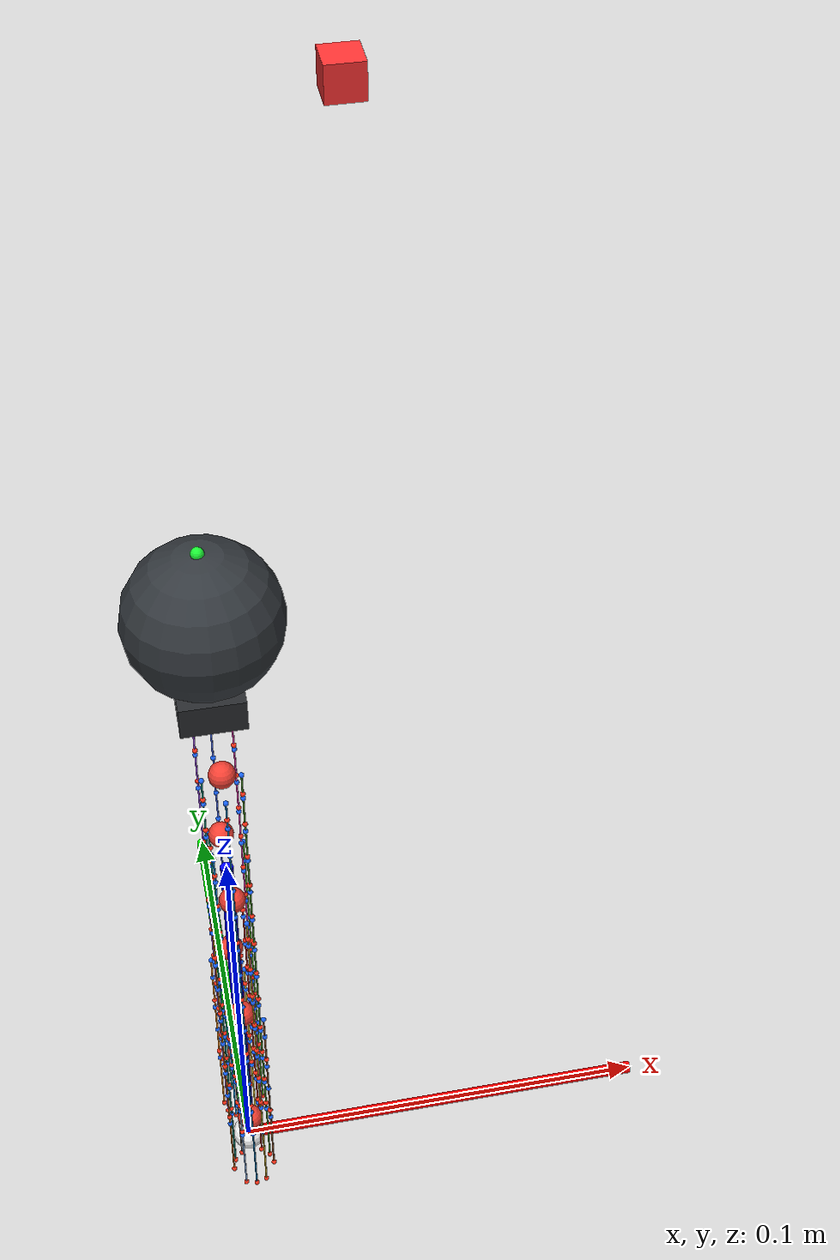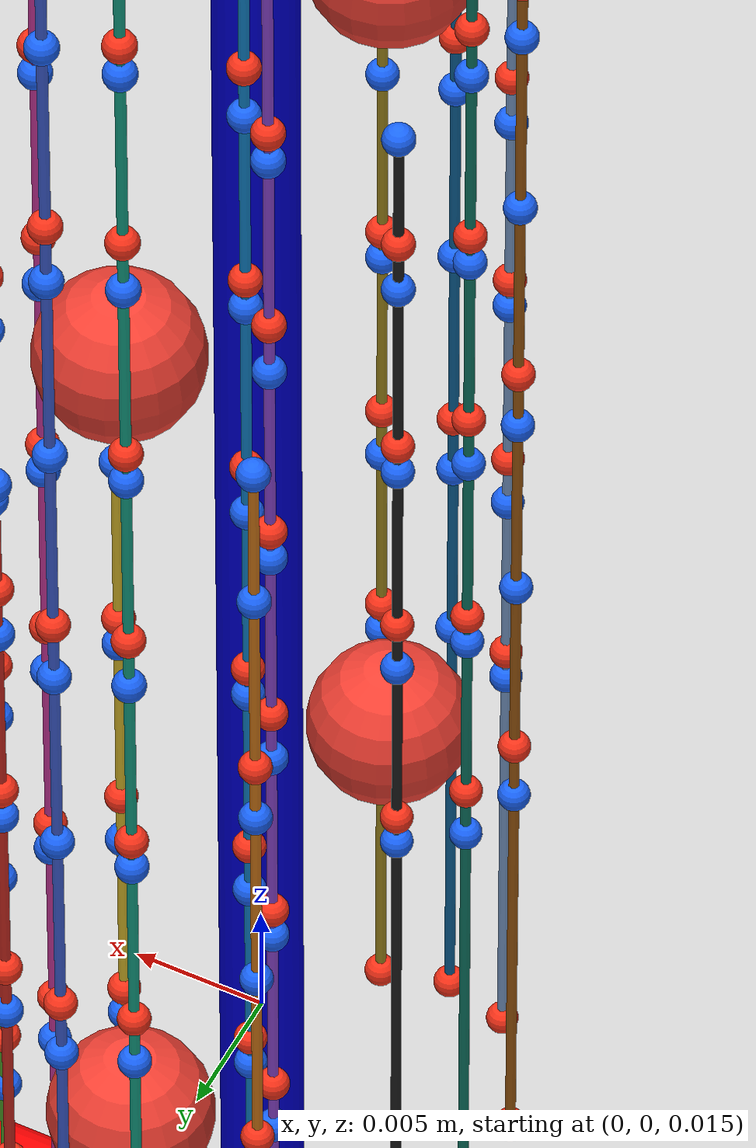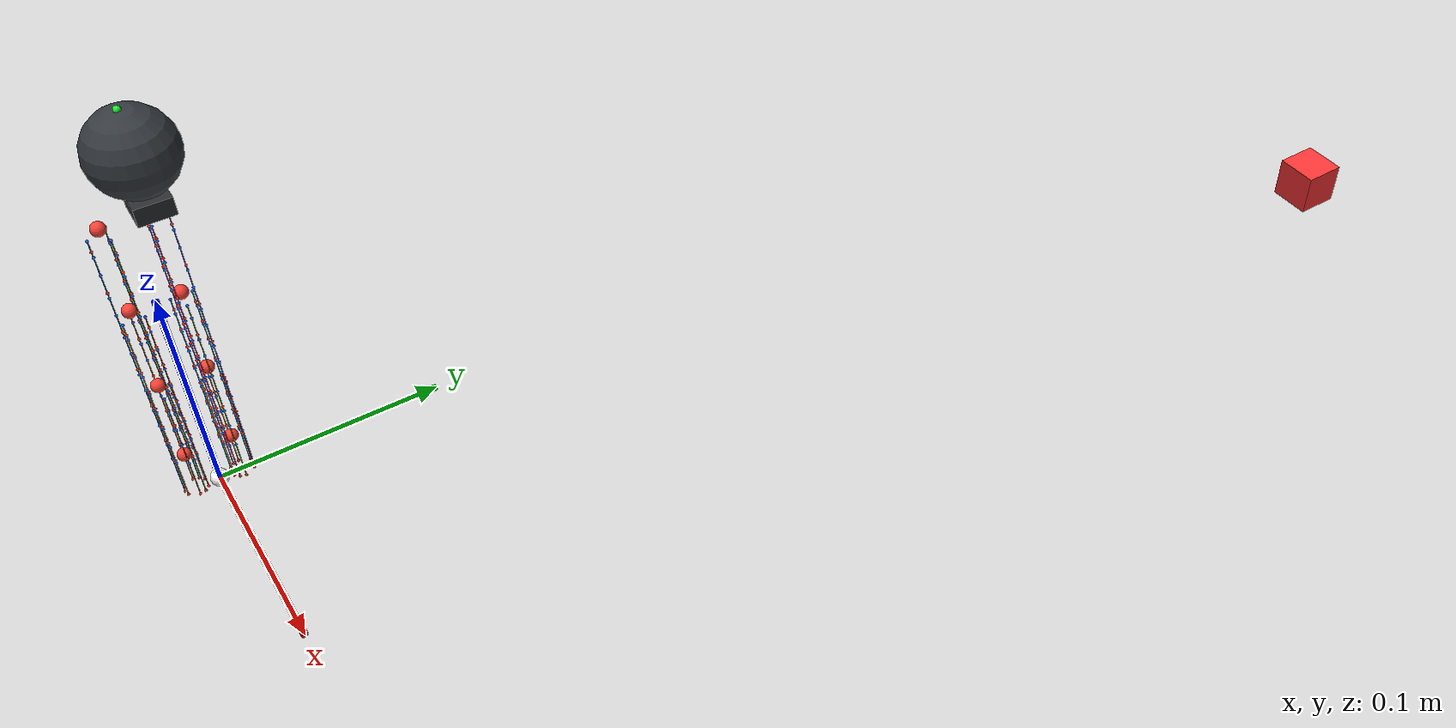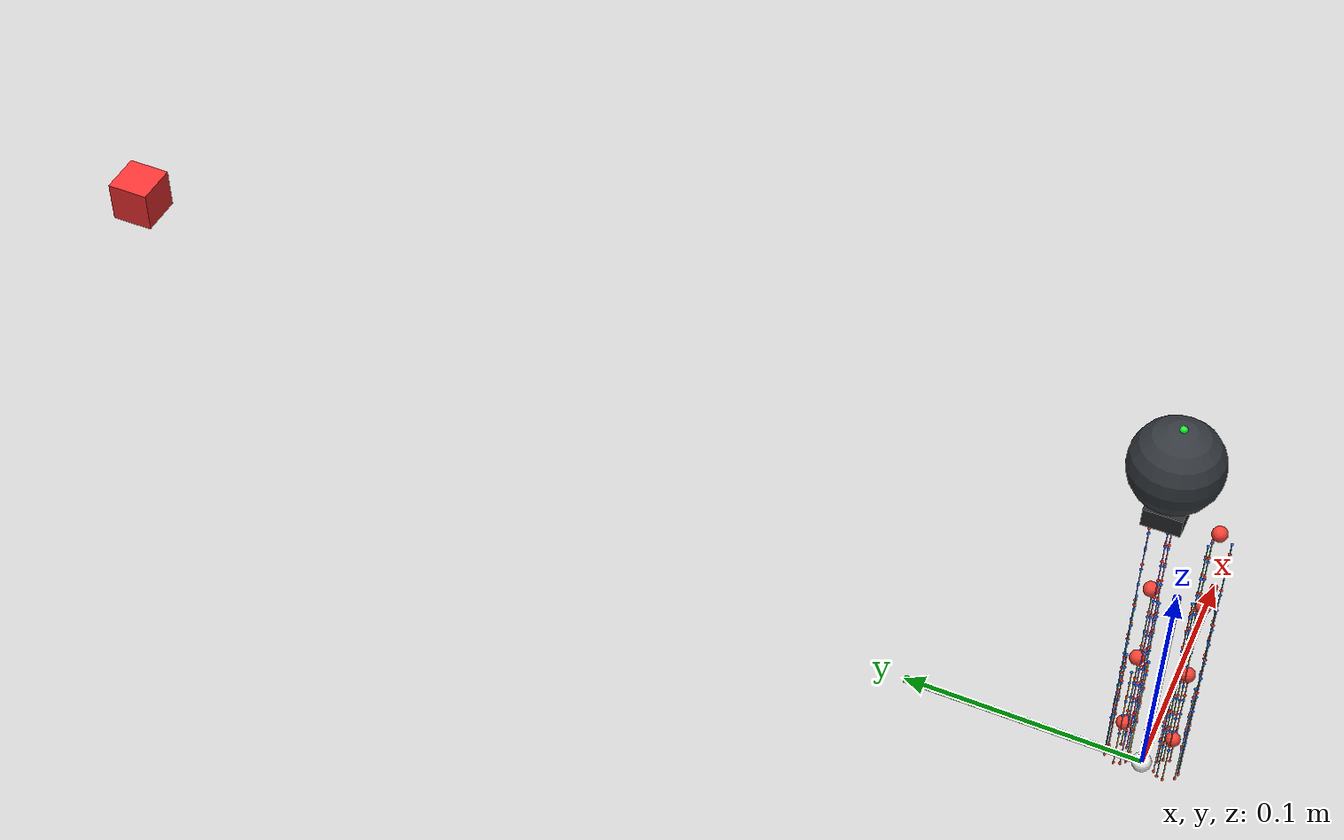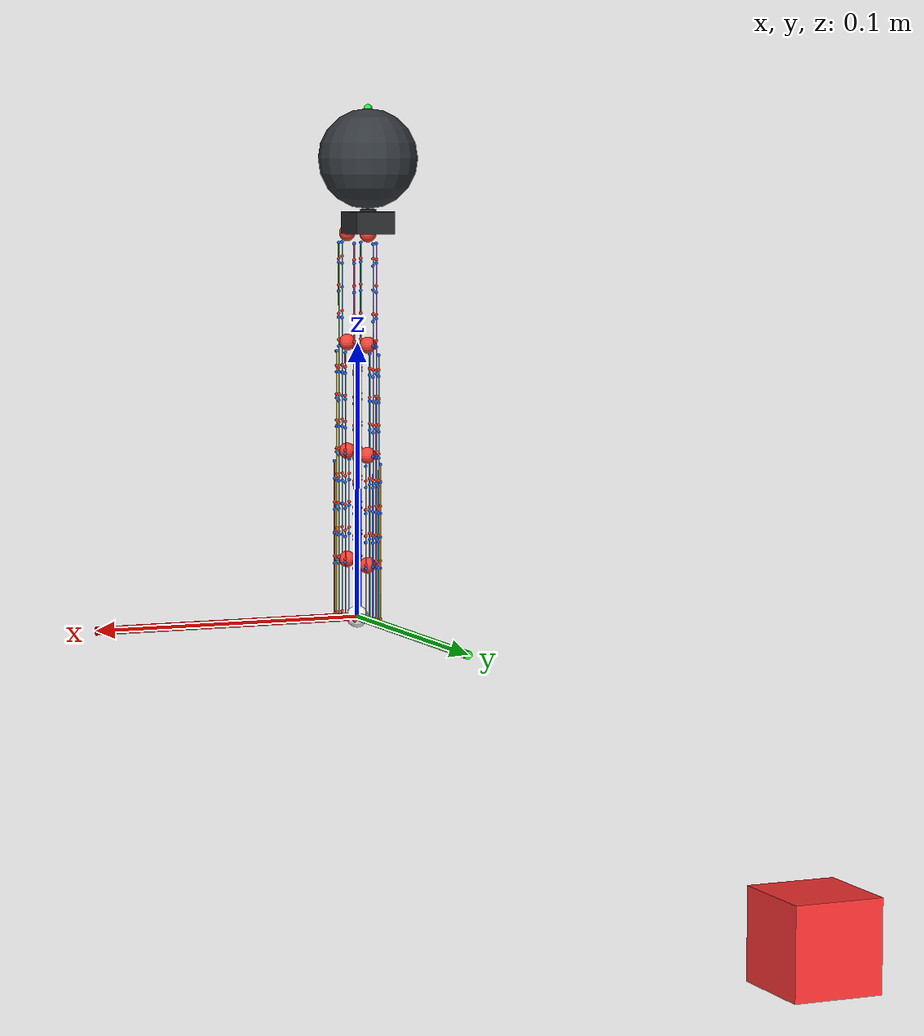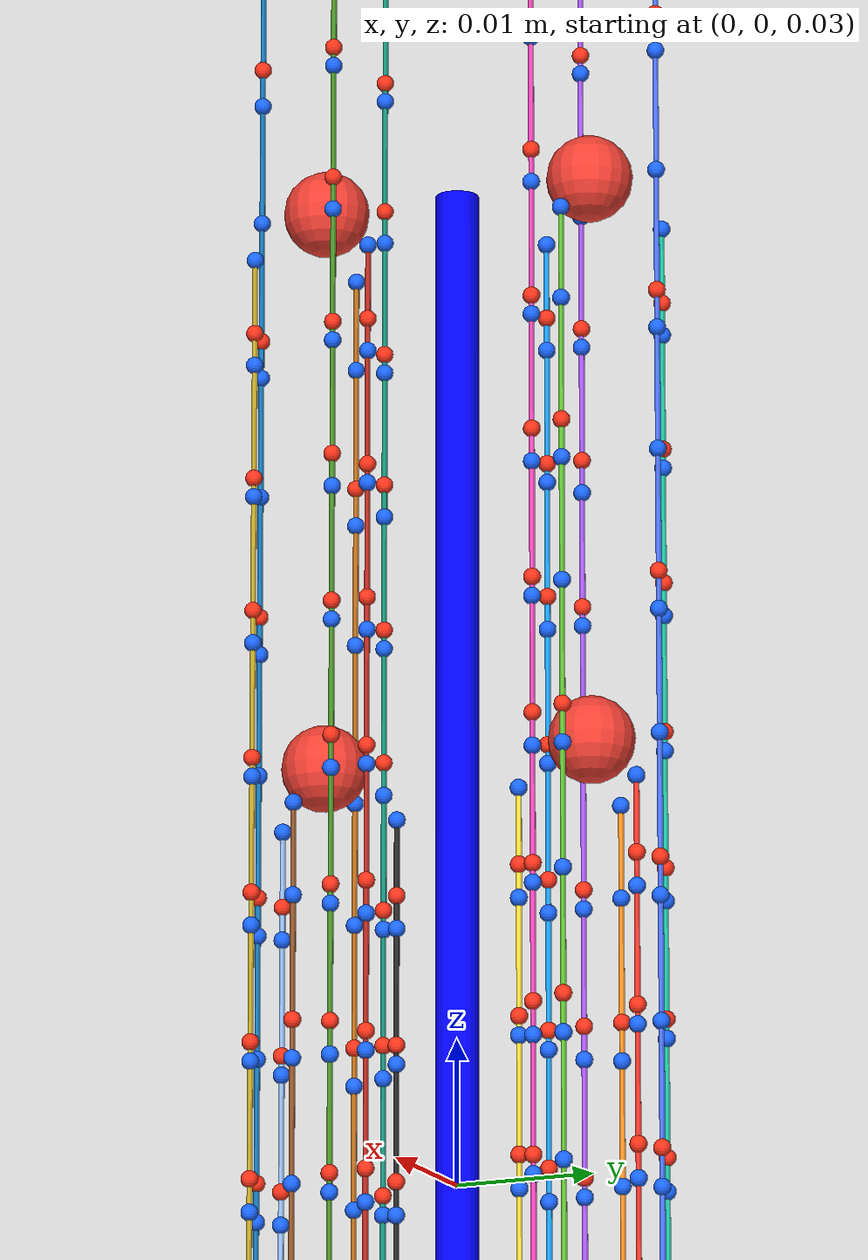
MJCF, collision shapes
<mujoco model="dual_three_segment_arm">
  <compiler angle="radian" />
  <option timestep="0.001" integrator="implicitfast" iterations="50" gravity="0 0 0" />
  <visual>
    <global azimuth="210" elevation="-45" offwidth="1080" offheight="720" />
    <headlight ambient="0.32 0.32 0.32" diffuse="0.78 0.78 0.78" specular="0.45 0.45 0.45" />
    <map znear="0.001" zfar="2" />
    <quality shadowsize="2048" />
  </visual>
  <asset>
    <mesh name="shared_base_visual_mesh" file="../../assets/meshes/dual_arm/shared_base/dual_base_visual.stl" scale="0.001 0.001 0.001" />
    <mesh name="executor_base_visual_mesh" file="../../assets/meshes/dual_arm/executor/base_visual.stl" scale="0.001 0.001 0.001" />
    <mesh name="executor_segment_1_link_1_visual_mesh" file="../../assets/meshes/dual_arm/executor/segment_1_link_1_visual.stl" scale="0.001 0.001 0.001" />
    <mesh name="executor_segment_1_link_2_visual_mesh" file="../../assets/meshes/dual_arm/executor/segment_1_link_2_visual.stl" scale="0.001 0.001 0.001" />
    <mesh name="executor_segment_1_link_3_visual_mesh" file="../../assets/meshes/dual_arm/executor/segment_1_link_3_visual.stl" scale="0.001 0.001 0.001" />
    <mesh name="executor_segment_1_link_4_visual_mesh" file="../../assets/meshes/dual_arm/executor/segment_1_link_4_visual.stl" scale="0.001 0.001 0.001" />
    <mesh name="executor_segment_2_link_1_visual_mesh" file="../../assets/meshes/dual_arm/executor/segment_2_link_1_visual.stl" scale="0.001 0.001 0.001" />
    <mesh name="executor_segment_2_link_2_visual_mesh" file="../../assets/meshes/dual_arm/executor/segment_2_link_2_visual.stl" scale="0.001 0.001 0.001" />
    <mesh name="executor_segment_2_link_3_visual_mesh" file="../../assets/meshes/dual_arm/executor/segment_2_link_3_visual.stl" scale="0.001 0.001 0.001" />
    <mesh name="executor_segment_2_link_4_visual_mesh" file="../../assets/meshes/dual_arm/executor/segment_2_link_4_visual.stl" scale="0.001 0.001 0.001" />
    <mesh name="executor_segment_3_link_1_visual_mesh" file="../../assets/meshes/dual_arm/executor/segment_3_link_1_visual.stl" scale="0.001 0.001 0.001" />
    <mesh name="executor_segment_3_link_2_visual_mesh" file="../../assets/meshes/dual_arm/executor/segment_3_link_2_visual.stl" scale="0.001 0.001 0.001" />
    <mesh name="executor_segment_3_link_3_visual_mesh" file="../../assets/meshes/dual_arm/executor/segment_3_link_3_visual.stl" scale="0.001 0.001 0.001" />
    <mesh name="executor_segment_3_link_4_visual_mesh" file="../../assets/meshes/dual_arm/executor/segment_3_link_4_visual.stl" scale="0.001 0.001 0.001" />
    <mesh name="observer_base_visual_mesh" file="../../assets/meshes/dual_arm/observer/base_visual.stl" scale="0.001 0.001 0.001" />
    <mesh name="observer_segment_1_link_1_visual_mesh" file="../../assets/meshes/dual_arm/observer/segment_1_link_1_visual.stl" scale="0.001 0.001 0.001" />
    <mesh name="observer_segment_1_link_2_visual_mesh" file="../../assets/meshes/dual_arm/observer/segment_1_link_2_visual.stl" scale="0.001 0.001 0.001" />
    <mesh name="observer_segment_1_link_3_visual_mesh" file="../../assets/meshes/dual_arm/observer/segment_1_link_3_visual.stl" scale="0.001 0.001 0.001" />
    <mesh name="observer_segment_1_link_4_visual_mesh" file="../../assets/meshes/dual_arm/observer/segment_1_link_4_visual.stl" scale="0.001 0.001 0.001" />
    <mesh name="observer_segment_2_link_1_visual_mesh" file="../../assets/meshes/dual_arm/observer/segment_2_link_1_visual.stl" scale="0.001 0.001 0.001" />
    <mesh name="observer_segment_2_link_2_visual_mesh" file="../../assets/meshes/dual_arm/observer/segment_2_link_2_visual.stl" scale="0.001 0.001 0.001" />
    <mesh name="observer_segment_2_link_3_visual_mesh" file="../../assets/meshes/dual_arm/observer/segment_2_link_3_visual.stl" scale="0.001 0.001 0.001" />
    <mesh name="observer_segment_2_link_4_visual_mesh" file="../../assets/meshes/dual_arm/observer/segment_2_link_4_visual.stl" scale="0.001 0.001 0.001" />
    <mesh name="observer_segment_3_link_1_visual_mesh" file="../../assets/meshes/dual_arm/observer/segment_3_link_1_visual.stl" scale="0.001 0.001 0.001" />
    <mesh name="observer_segment_3_link_2_visual_mesh" file="../../assets/meshes/dual_arm/observer/segment_3_link_2_visual.stl" scale="0.001 0.001 0.001" />
    <mesh name="observer_segment_3_link_3_visual_mesh" file="../../assets/meshes/dual_arm/observer/segment_3_link_3_visual.stl" scale="0.001 0.001 0.001" />
    <mesh name="observer_segment_3_link_4_visual_mesh" file="../../assets/meshes/dual_arm/observer/segment_3_link_4_visual.stl" scale="0.001 0.001 0.001" />
    <mesh name="engine_visual_mesh_part_1" file="engine_visual_mujoco_part_01.stl" scale="0.001 0.001 0.001" />
    <mesh name="engine_visual_mesh_part_2" file="engine_visual_mujoco_part_02.stl" scale="0.001 0.001 0.001" />
    <material name="engine_silver" rgba="0.66 0.68 0.71 1" emission="0" specular="0.72" shininess="0.48" />
  </asset>
  <default>
    <joint damping="0.1" armature="0.0001" limited="true" range="-0.261799387799 0.261799387799" stiffness="0.01" springref="0" />
    <geom type="capsule" size="0.004" density="1100" rgba="0.2 0.45 0.85 1" group="0" />
    <site size="0.003" rgba="0.95 0.25 0.2 1" />
  </default>
  <worldbody>
    <body name="mobile_base" pos="0 0 0" quat="1 0 0 0">
      <inertial pos="0 0 0" mass="1" diaginertia="0.001 0.001 0.001" />
      <freejoint name="mobile_base_freejoint" />
      <site name="mobile_base_frame" type="sphere" pos="0 0 0" size="0.002" rgba="0.2 0.6 1 0.8" group="2" />
      <site name="dual_arm_mount" type="sphere" pos="0 0 0" quat="1 0 0 0" size="0.002" rgba="0.95 0.55 0.12 0.85" group="2" />
      <body name="dual_mobile_base" pos="0 0 0" quat="1 0 0 0">
        <site name="dual_mobile_base_frame" pos="0 0 0" quat="1 0 0 0" />
        <geom name="dual_mobile_base_visual" type="mesh" mesh="shared_base_visual_mesh" pos="-0 -0 -0" contype="0" conaffinity="0" density="0" group="1" />
        <body name="executor_base" pos="0 0.01 0.02" quat="1 0 0 0">
          <site name="executor_base_site" pos="0 0 0" quat="1 0 0 0" />
          <site name="executor_base_hole_01_in" pos="0.005 0 -0.02" size="0.0006" rgba="1 0.2 0.1 1" />
          <site name="executor_base_hole_01_out" pos="0.005 0 -0.00133975" size="0.0006" rgba="0.1 0.4 1 1" />
          <site name="executor_base_hole_03_in" pos="0.0025 0.00433013 -0.02" size="0.0006" rgba="1 0.2 0.1 1" />
          <site name="executor_base_hole_03_out" pos="0.0025 0.00433013 -0.00066987" size="0.0006" rgba="0.1 0.4 1 1" />
          <site name="executor_base_hole_04_in" pos="0 0.005 -0.02" size="0.0006" rgba="1 0.2 0.1 1" />
          <site name="executor_base_hole_04_out" pos="0 0.005 0" size="0.0006" rgba="0.1 0.4 1 1" />
          <site name="executor_base_hole_05_in" pos="-0.0025 0.00433013 -0.02" size="0.0006" rgba="1 0.2 0.1 1" />
          <site name="executor_base_hole_05_out" pos="-0.0025 0.00433013 -0.00066987" size="0.0006" rgba="0.1 0.4 1 1" />
          <site name="executor_base_hole_07_in" pos="-0.005 0 -0.02" size="0.0006" rgba="1 0.2 0.1 1" />
          <site name="executor_base_hole_07_out" pos="-0.005 0 -0.00133975" size="0.0006" rgba="0.1 0.4 1 1" />
          <site name="executor_base_hole_08_in" pos="-0.00433013 -0.0025 -0.02" size="0.0006" rgba="1 0.2 0.1 1" />
          <site name="executor_base_hole_08_out" pos="-0.00433013 -0.0025 -0.00116025" size="0.0006" rgba="0.1 0.4 1 1" />
          <site name="executor_base_hole_09_in" pos="-0.0025 -0.00433013 -0.02" size="0.0006" rgba="1 0.2 0.1 1" />
          <site name="executor_base_hole_09_out" pos="-0.0025 -0.00433013 -0.00066987" size="0.0006" rgba="0.1 0.4 1 1" />
          <site name="executor_base_hole_11_in" pos="0.0025 -0.00433013 -0.02" size="0.0006" rgba="1 0.2 0.1 1" />
          <site name="executor_base_hole_11_out" pos="0.0025 -0.00433013 -0.00066987" size="0.0006" rgba="0.1 0.4 1 1" />
          <site name="executor_base_hole_12_in" pos="0.00433013 -0.0025 -0.02" size="0.0006" rgba="1 0.2 0.1 1" />
          <site name="executor_base_hole_12_out" pos="0.00433013 -0.0025 -0.00116025" size="0.0006" rgba="0.1 0.4 1 1" />
          <geom name="executor_base_visual" type="mesh" mesh="executor_base_visual_mesh" pos="-0 -0.01 -0.02" contype="0" conaffinity="0" density="0" group="1" />
          <body name="executor_segment_1_link_1" pos="0 0 0">
            <joint name="executor_segment_1_link_1_y" type="hinge" axis="0 1 0" stiffness="0.0109589041096" />
            <geom name="executor_segment_1_link_1_collision" type="capsule" fromto="0 0 0 0 0 0.01" size="0.00625" group="0" mass="0.0024748225" contype="0" conaffinity="0" rgba="0.2 0.45 0.85 0" />
            <geom name="executor_segment_1_link_1_visual" type="mesh" mesh="executor_segment_1_link_1_visual_mesh" pos="-0 -0.01 -0.02" contype="0" conaffinity="0" density="0" group="1" />
            <site name="executor_segment_1_link_1_hole_01_in" pos="0.005 0 0.00133975" size="0.0006" rgba="1 0.2 0.1 1" />
            <site name="executor_segment_1_link_1_hole_03_in" pos="0.0025 0.00433013 0.00066987" size="0.0006" rgba="1 0.2 0.1 1" />
            <site name="executor_segment_1_link_1_hole_04_in" pos="0 0.005 0" size="0.0006" rgba="1 0.2 0.1 1" />
            <site name="executor_segment_1_link_1_hole_05_in" pos="-0.0025 0.00433013 0.00066987" size="0.0006" rgba="1 0.2 0.1 1" />
            <site name="executor_segment_1_link_1_hole_07_in" pos="-0.005 0 0.00133975" size="0.0006" rgba="1 0.2 0.1 1" />
            <site name="executor_segment_1_link_1_hole_08_in" pos="-0.00433013 -0.0025 0.00116025" size="0.0006" rgba="1 0.2 0.1 1" />
            <site name="executor_segment_1_link_1_hole_09_in" pos="-0.0025 -0.00433013 0.00066987" size="0.0006" rgba="1 0.2 0.1 1" />
            <site name="executor_segment_1_link_1_hole_11_in" pos="0.0025 -0.00433013 0.00066987" size="0.0006" rgba="1 0.2 0.1 1" />
            <site name="executor_segment_1_link_1_hole_12_in" pos="0.00433013 -0.0025 0.00116025" size="0.0006" rgba="1 0.2 0.1 1" />
            <site name="executor_segment_1_link_1_hole_01_out" pos="0.005 0 0.01" size="0.0006" rgba="0.1 0.4 1 1" />
            <site name="executor_segment_1_link_1_hole_03_out" pos="0.0025 0.00433013 0.00883975" size="0.0006" rgba="0.1 0.4 1 1" />
            <site name="executor_segment_1_link_1_hole_04_out" pos="0 0.005 0.00866025" size="0.0006" rgba="0.1 0.4 1 1" />
            <site name="executor_segment_1_link_1_hole_05_out" pos="-0.0025 0.00433013 0.00883975" size="0.0006" rgba="0.1 0.4 1 1" />
            <site name="executor_segment_1_link_1_hole_07_out" pos="-0.005 0 0.01" size="0.0006" rgba="0.1 0.4 1 1" />
            <site name="executor_segment_1_link_1_hole_08_out" pos="-0.00433013 -0.0025 0.00933013" size="0.0006" rgba="0.1 0.4 1 1" />
            <site name="executor_segment_1_link_1_hole_09_out" pos="-0.0025 -0.00433013 0.00883975" size="0.0006" rgba="0.1 0.4 1 1" />
            <site name="executor_segment_1_link_1_hole_11_out" pos="0.0025 -0.00433013 0.00883975" size="0.0006" rgba="0.1 0.4 1 1" />
            <site name="executor_segment_1_link_1_hole_12_out" pos="0.00433013 -0.0025 0.00933013" size="0.0006" rgba="0.1 0.4 1 1" />
            <body name="executor_segment_1_link_2" pos="0 0 0.01">
              <joint name="executor_segment_1_link_2_x" type="hinge" axis="1 0 0" stiffness="0.0109589041096" />
              <geom name="executor_segment_1_link_2_collision" type="capsule" fromto="0 0 0 0 0 0.01" size="0.00625" group="0" mass="0.0024748225" contype="0" conaffinity="0" rgba="0.2 0.45 0.85 0" />
              <geom name="executor_segment_1_link_2_visual" type="mesh" mesh="executor_segment_1_link_2_visual_mesh" pos="-0 -0.01 -0.03" contype="0" conaffinity="0" density="0" group="1" />
              <site name="executor_segment_1_link_2_hole_01_in" pos="0.005 0 0" size="0.0006" rgba="1 0.2 0.1 1" />
              <site name="executor_segment_1_link_2_hole_03_in" pos="0.0025 0.00433013 0.00116025" size="0.0006" rgba="1 0.2 0.1 1" />
              <site name="executor_segment_1_link_2_hole_04_in" pos="0 0.005 0.00133975" size="0.0006" rgba="1 0.2 0.1 1" />
              <site name="executor_segment_1_link_2_hole_05_in" pos="-0.0025 0.00433013 0.00116025" size="0.0006" rgba="1 0.2 0.1 1" />
              <site name="executor_segment_1_link_2_hole_07_in" pos="-0.005 0 0" size="0.0006" rgba="1 0.2 0.1 1" />
              <site name="executor_segment_1_link_2_hole_08_in" pos="-0.00433013 -0.0025 0.00066987" size="0.0006" rgba="1 0.2 0.1 1" />
              <site name="executor_segment_1_link_2_hole_09_in" pos="-0.0025 -0.00433013 0.00116025" size="0.0006" rgba="1 0.2 0.1 1" />
              <site name="executor_segment_1_link_2_hole_11_in" pos="0.0025 -0.00433013 0.00116025" size="0.0006" rgba="1 0.2 0.1 1" />
              <site name="executor_segment_1_link_2_hole_12_in" pos="0.00433013 -0.0025 0.00066987" size="0.0006" rgba="1 0.2 0.1 1" />
              <site name="executor_segment_1_link_2_hole_01_out" pos="0.005 0 0.00866025" size="0.0006" rgba="0.1 0.4 1 1" />
              <site name="executor_segment_1_link_2_hole_03_out" pos="0.0025 0.00433013 0.00933013" size="0.0006" rgba="0.1 0.4 1 1" />
              <site name="executor_segment_1_link_2_hole_04_out" pos="0 0.005 0.01" size="0.0006" rgba="0.1 0.4 1 1" />
              <site name="executor_segment_1_link_2_hole_05_out" pos="-0.0025 0.00433013 0.00933013" size="0.0006" rgba="0.1 0.4 1 1" />
              <site name="executor_segment_1_link_2_hole_07_out" pos="-0.005 0 0.00866025" size="0.0006" rgba="0.1 0.4 1 1" />
              <site name="executor_segment_1_link_2_hole_08_out" pos="-0.00433013 -0.0025 0.00883975" size="0.0006" rgba="0.1 0.4 1 1" />
              <site name="executor_segment_1_link_2_hole_09_out" pos="-0.0025 -0.00433013 0.00933013" size="0.0006" rgba="0.1 0.4 1 1" />
              <site name="executor_segment_1_link_2_hole_11_out" pos="0.0025 -0.00433013 0.00933013" size="0.0006" rgba="0.1 0.4 1 1" />
              <site name="executor_segment_1_link_2_hole_12_out" pos="0.00433013 -0.0025 0.00883975" size="0.0006" rgba="0.1 0.4 1 1" />
              <body name="executor_segment_1_link_3" pos="0 0 0.01">
                <joint name="executor_segment_1_link_3_y" type="hinge" axis="0 1 0" stiffness="0.0109589041096" />
                <geom name="executor_segment_1_link_3_collision" type="capsule" fromto="0 0 0 0 0 0.01" size="0.00625" group="0" mass="0.0024748225" contype="0" conaffinity="0" rgba="0.2 0.45 0.85 0" />
                <geom name="executor_segment_1_link_3_visual" type="mesh" mesh="executor_segment_1_link_3_visual_mesh" pos="-0 -0.01 -0.04" contype="0" conaffinity="0" density="0" group="1" />
                <site name="executor_segment_1_link_3_hole_01_in" pos="0.005 0 0.00133975" size="0.0006" rgba="1 0.2 0.1 1" />
                <site name="executor_segment_1_link_3_hole_03_in" pos="0.0025 0.00433013 0.00066987" size="0.0006" rgba="1 0.2 0.1 1" />
                <site name="executor_segment_1_link_3_hole_04_in" pos="0 0.005 0" size="0.0006" rgba="1 0.2 0.1 1" />
                <site name="executor_segment_1_link_3_hole_05_in" pos="-0.0025 0.00433013 0.00066987" size="0.0006" rgba="1 0.2 0.1 1" />
                <site name="executor_segment_1_link_3_hole_07_in" pos="-0.005 0 0.00133975" size="0.0006" rgba="1 0.2 0.1 1" />
                <site name="executor_segment_1_link_3_hole_08_in" pos="-0.00433013 -0.0025 0.00116025" size="0.0006" rgba="1 0.2 0.1 1" />
                <site name="executor_segment_1_link_3_hole_09_in" pos="-0.0025 -0.00433013 0.00066987" size="0.0006" rgba="1 0.2 0.1 1" />
                <site name="executor_segment_1_link_3_hole_11_in" pos="0.0025 -0.00433013 0.00066987" size="0.0006" rgba="1 0.2 0.1 1" />
                <site name="executor_segment_1_link_3_hole_12_in" pos="0.00433013 -0.0025 0.00116025" size="0.0006" rgba="1 0.2 0.1 1" />
                <site name="executor_segment_1_link_3_hole_01_out" pos="0.005 0 0.01" size="0.0006" rgba="0.1 0.4 1 1" />
                <site name="executor_segment_1_link_3_hole_03_out" pos="0.0025 0.00433013 0.00883975" size="0.0006" rgba="0.1 0.4 1 1" />
                <site name="executor_segment_1_link_3_hole_04_out" pos="0 0.005 0.00866025" size="0.0006" rgba="0.1 0.4 1 1" />
                <site name="executor_segment_1_link_3_hole_05_out" pos="-0.0025 0.00433013 0.00883975" size="0.0006" rgba="0.1 0.4 1 1" />
                <site name="executor_segment_1_link_3_hole_07_out" pos="-0.005 0 0.01" size="0.0006" rgba="0.1 0.4 1 1" />
                <site name="executor_segment_1_link_3_hole_08_out" pos="-0.00433013 -0.0025 0.00933013" size="0.0006" rgba="0.1 0.4 1 1" />
                <site name="executor_segment_1_link_3_hole_09_out" pos="-0.0025 -0.00433013 0.00883975" size="0.0006" rgba="0.1 0.4 1 1" />
                <site name="executor_segment_1_link_3_hole_11_out" pos="0.0025 -0.00433013 0.00883975" size="0.0006" rgba="0.1 0.4 1 1" />
                <site name="executor_segment_1_link_3_hole_12_out" pos="0.00433013 -0.0025 0.00933013" size="0.0006" rgba="0.1 0.4 1 1" />
                <body name="executor_segment_1_link_4" pos="0 0 0.01">
                  <joint name="executor_segment_1_link_4_x" type="hinge" axis="1 0 0" stiffness="0.0109589041096" />
                  <geom name="executor_segment_1_link_4_collision" type="capsule" fromto="0 0 0 0 0 0.01" size="0.00625" group="0" mass="0.0024748225" contype="0" conaffinity="0" rgba="0.2 0.45 0.85 0" />
                  <geom name="executor_segment_1_link_4_visual" type="mesh" mesh="executor_segment_1_link_4_visual_mesh" pos="-0 -0.01 -0.05" contype="0" conaffinity="0" density="0" group="1" />
                  <site name="executor_segment_1_tip" pos="0 0 0.01" quat="1 0 0 0" />
                  <site name="executor_segment_1_link_4_hole_01_in" pos="0.005 0 0" size="0.0006" rgba="1 0.2 0.1 1" />
                  <site name="executor_segment_1_link_4_hole_03_in" pos="0.0025 0.00433013 0.00116025" size="0.0006" rgba="1 0.2 0.1 1" />
                  <site name="executor_segment_1_link_4_hole_04_in" pos="0 0.005 0.00133975" size="0.0006" rgba="1 0.2 0.1 1" />
                  <site name="executor_segment_1_link_4_hole_05_in" pos="-0.0025 0.00433013 0.00116025" size="0.0006" rgba="1 0.2 0.1 1" />
                  <site name="executor_segment_1_link_4_hole_07_in" pos="-0.005 0 0" size="0.0006" rgba="1 0.2 0.1 1" />
                  <site name="executor_segment_1_link_4_hole_08_in" pos="-0.00433013 -0.0025 0.00066987" size="0.0006" rgba="1 0.2 0.1 1" />
                  <site name="executor_segment_1_link_4_hole_09_in" pos="-0.0025 -0.00433013 0.00116025" size="0.0006" rgba="1 0.2 0.1 1" />
                  <site name="executor_segment_1_link_4_hole_11_in" pos="0.0025 -0.00433013 0.00116025" size="0.0006" rgba="1 0.2 0.1 1" />
                  <site name="executor_segment_1_link_4_hole_12_in" pos="0.00433013 -0.0025 0.00066987" size="0.0006" rgba="1 0.2 0.1 1" />
                  <site name="executor_segment_1_link_4_hole_01_out" pos="0.005 0 0.00866025" size="0.0006" rgba="0.1 0.4 1 1" />
                  <site name="executor_segment_1_link_4_hole_03_out" pos="0.0025 0.00433013 0.0065" size="0.0006" rgba="0.1 0.4 1 1" />
                  <site name="executor_segment_1_link_4_hole_04_out" pos="0 0.005 0.01" size="0.0006" rgba="0.1 0.4 1 1" />
                  <site name="executor_segment_1_link_4_hole_05_out" pos="-0.0025 0.00433013 0.00933013" size="0.0006" rgba="0.1 0.4 1 1" />
                  <site name="executor_segment_1_link_4_hole_07_out" pos="-0.005 0 0.0065" size="0.0006" rgba="0.1 0.4 1 1" />
                  <site name="executor_segment_1_link_4_hole_08_out" pos="-0.00433013 -0.0025 0.00883975" size="0.0006" rgba="0.1 0.4 1 1" />
                  <site name="executor_segment_1_link_4_hole_09_out" pos="-0.0025 -0.00433013 0.00933013" size="0.0006" rgba="0.1 0.4 1 1" />
                  <site name="executor_segment_1_link_4_hole_11_out" pos="0.0025 -0.00433013 0.0065" size="0.0006" rgba="0.1 0.4 1 1" />
                  <site name="executor_segment_1_link_4_hole_12_out" pos="0.00433013 -0.0025 0.00883975" size="0.0006" rgba="0.1 0.4 1 1" />
                  <body name="executor_segment_2_link_1" pos="0 0 0.01">
                    <joint name="executor_segment_2_link_1_y" type="hinge" axis="0 1 0" stiffness="0.0109589041096" />
                    <geom name="executor_segment_2_link_1_collision" type="capsule" fromto="0 0 0 0 0 0.01" size="0.00625" group="0" mass="0.0024748225" contype="0" conaffinity="0" rgba="0.2 0.45 0.85 0" />
                    <geom name="executor_segment_2_link_1_visual" type="mesh" mesh="executor_segment_2_link_1_visual_mesh" pos="-0 -0.01 -0.06" contype="0" conaffinity="0" density="0" group="1" />
                    <site name="executor_segment_2_link_1_hole_01_in" pos="0.005 0 0.00133975" size="0.0006" rgba="1 0.2 0.1 1" />
                    <site name="executor_segment_2_link_1_hole_04_in" pos="0 0.005 0" size="0.0006" rgba="1 0.2 0.1 1" />
                    <site name="executor_segment_2_link_1_hole_05_in" pos="-0.0025 0.00433013 0.00066987" size="0.0006" rgba="1 0.2 0.1 1" />
                    <site name="executor_segment_2_link_1_hole_08_in" pos="-0.00433013 -0.0025 0.00116025" size="0.0006" rgba="1 0.2 0.1 1" />
                    <site name="executor_segment_2_link_1_hole_09_in" pos="-0.0025 -0.00433013 0.00066987" size="0.0006" rgba="1 0.2 0.1 1" />
                    <site name="executor_segment_2_link_1_hole_12_in" pos="0.00433013 -0.0025 0.00116025" size="0.0006" rgba="1 0.2 0.1 1" />
                    <site name="executor_segment_2_link_1_hole_01_out" pos="0.005 0 0.01" size="0.0006" rgba="0.1 0.4 1 1" />
                    <site name="executor_segment_2_link_1_hole_04_out" pos="0 0.005 0.00866025" size="0.0006" rgba="0.1 0.4 1 1" />
                    <site name="executor_segment_2_link_1_hole_05_out" pos="-0.0025 0.00433013 0.00883975" size="0.0006" rgba="0.1 0.4 1 1" />
                    <site name="executor_segment_2_link_1_hole_08_out" pos="-0.00433013 -0.0025 0.00933013" size="0.0006" rgba="0.1 0.4 1 1" />
                    <site name="executor_segment_2_link_1_hole_09_out" pos="-0.0025 -0.00433013 0.00883975" size="0.0006" rgba="0.1 0.4 1 1" />
                    <site name="executor_segment_2_link_1_hole_12_out" pos="0.00433013 -0.0025 0.00933013" size="0.0006" rgba="0.1 0.4 1 1" />
                    <body name="executor_segment_2_link_2" pos="0 0 0.01">
                      <joint name="executor_segment_2_link_2_x" type="hinge" axis="1 0 0" stiffness="0.0109589041096" />
                      <geom name="executor_segment_2_link_2_collision" type="capsule" fromto="0 0 0 0 0 0.01" size="0.00625" group="0" mass="0.0024748225" contype="0" conaffinity="0" rgba="0.2 0.45 0.85 0" />
                      <geom name="executor_segment_2_link_2_visual" type="mesh" mesh="executor_segment_2_link_2_visual_mesh" pos="-0 -0.01 -0.07" contype="0" conaffinity="0" density="0" group="1" />
                      <site name="executor_segment_2_link_2_hole_01_in" pos="0.005 0 0" size="0.0006" rgba="1 0.2 0.1 1" />
                      <site name="executor_segment_2_link_2_hole_04_in" pos="0 0.005 0.00133975" size="0.0006" rgba="1 0.2 0.1 1" />
                      <site name="executor_segment_2_link_2_hole_05_in" pos="-0.0025 0.00433013 0.00116025" size="0.0006" rgba="1 0.2 0.1 1" />
                      <site name="executor_segment_2_link_2_hole_08_in" pos="-0.00433013 -0.0025 0.00066987" size="0.0006" rgba="1 0.2 0.1 1" />
                      <site name="executor_segment_2_link_2_hole_09_in" pos="-0.0025 -0.00433013 0.00116025" size="0.0006" rgba="1 0.2 0.1 1" />
                      <site name="executor_segment_2_link_2_hole_12_in" pos="0.00433013 -0.0025 0.00066987" size="0.0006" rgba="1 0.2 0.1 1" />
                      <site name="executor_segment_2_link_2_hole_01_out" pos="0.005 0 0.00866025" size="0.0006" rgba="0.1 0.4 1 1" />
                      <site name="executor_segment_2_link_2_hole_04_out" pos="0 0.005 0.01" size="0.0006" rgba="0.1 0.4 1 1" />
                      <site name="executor_segment_2_link_2_hole_05_out" pos="-0.0025 0.00433013 0.00933013" size="0.0006" rgba="0.1 0.4 1 1" />
                      <site name="executor_segment_2_link_2_hole_08_out" pos="-0.00433013 -0.0025 0.00883975" size="0.0006" rgba="0.1 0.4 1 1" />
                      <site name="executor_segment_2_link_2_hole_09_out" pos="-0.0025 -0.00433013 0.00933013" size="0.0006" rgba="0.1 0.4 1 1" />
                      <site name="executor_segment_2_link_2_hole_12_out" pos="0.00433013 -0.0025 0.00883975" size="0.0006" rgba="0.1 0.4 1 1" />
                      <body name="executor_segment_2_link_3" pos="0 0 0.01">
                        <joint name="executor_segment_2_link_3_y" type="hinge" axis="0 1 0" stiffness="0.0109589041096" />
                        <geom name="executor_segment_2_link_3_collision" type="capsule" fromto="0 0 0 0 0 0.01" size="0.00625" group="0" mass="0.0024748225" contype="0" conaffinity="0" rgba="0.2 0.45 0.85 0" />
                        <geom name="executor_segment_2_link_3_visual" type="mesh" mesh="executor_segment_2_link_3_visual_mesh" pos="-0 -0.01 -0.08" contype="0" conaffinity="0" density="0" group="1" />
                        <site name="executor_segment_2_link_3_hole_01_in" pos="0.005 0 0.00133975" size="0.0006" rgba="1 0.2 0.1 1" />
                        <site name="executor_segment_2_link_3_hole_04_in" pos="0 0.005 0" size="0.0006" rgba="1 0.2 0.1 1" />
                        <site name="executor_segment_2_link_3_hole_05_in" pos="-0.0025 0.00433013 0.00066987" size="0.0006" rgba="1 0.2 0.1 1" />
                        <site name="executor_segment_2_link_3_hole_08_in" pos="-0.00433013 -0.0025 0.00116025" size="0.0006" rgba="1 0.2 0.1 1" />
                        <site name="executor_segment_2_link_3_hole_09_in" pos="-0.0025 -0.00433013 0.00066987" size="0.0006" rgba="1 0.2 0.1 1" />
                        <site name="executor_segment_2_link_3_hole_12_in" pos="0.00433013 -0.0025 0.00116025" size="0.0006" rgba="1 0.2 0.1 1" />
                        <site name="executor_segment_2_link_3_hole_01_out" pos="0.005 0 0.01" size="0.0006" rgba="0.1 0.4 1 1" />
                        <site name="executor_segment_2_link_3_hole_04_out" pos="0 0.005 0.00866025" size="0.0006" rgba="0.1 0.4 1 1" />
                        <site name="executor_segment_2_link_3_hole_05_out" pos="-0.0025 0.00433013 0.00883975" size="0.0006" rgba="0.1 0.4 1 1" />
                        <site name="executor_segment_2_link_3_hole_08_out" pos="-0.00433013 -0.0025 0.00933013" size="0.0006" rgba="0.1 0.4 1 1" />
                        <site name="executor_segment_2_link_3_hole_09_out" pos="-0.0025 -0.00433013 0.00883975" size="0.0006" rgba="0.1 0.4 1 1" />
                        <site name="executor_segment_2_link_3_hole_12_out" pos="0.00433013 -0.0025 0.00933013" size="0.0006" rgba="0.1 0.4 1 1" />
                        <body name="executor_segment_2_link_4" pos="0 0 0.01">
                          <joint name="executor_segment_2_link_4_x" type="hinge" axis="1 0 0" stiffness="0.0109589041096" />
                          <geom name="executor_segment_2_link_4_collision" type="capsule" fromto="0 0 0 0 0 0.01" size="0.00625" group="0" mass="0.0024748225" contype="0" conaffinity="0" rgba="0.2 0.45 0.85 0" />
                          <geom name="executor_segment_2_link_4_visual" type="mesh" mesh="executor_segment_2_link_4_visual_mesh" pos="-0 -0.01 -0.09" contype="0" conaffinity="0" density="0" group="1" />
                          <site name="executor_segment_2_tip" pos="0 0 0.01" quat="1 0 0 0" />
                          <site name="executor_segment_2_link_4_hole_01_in" pos="0.005 0 0" size="0.0006" rgba="1 0.2 0.1 1" />
                          <site name="executor_segment_2_link_4_hole_04_in" pos="0 0.005 0.00133975" size="0.0006" rgba="1 0.2 0.1 1" />
                          <site name="executor_segment_2_link_4_hole_05_in" pos="-0.0025 0.00433013 0.00116025" size="0.0006" rgba="1 0.2 0.1 1" />
                          <site name="executor_segment_2_link_4_hole_08_in" pos="-0.00433013 -0.0025 0.00066987" size="0.0006" rgba="1 0.2 0.1 1" />
                          <site name="executor_segment_2_link_4_hole_09_in" pos="-0.0025 -0.00433013 0.00116025" size="0.0006" rgba="1 0.2 0.1 1" />
                          <site name="executor_segment_2_link_4_hole_12_in" pos="0.00433013 -0.0025 0.00066987" size="0.0006" rgba="1 0.2 0.1 1" />
                          <site name="executor_segment_2_link_4_hole_01_out" pos="0.005 0 0.0065" size="0.0006" rgba="0.1 0.4 1 1" />
                          <site name="executor_segment_2_link_4_hole_04_out" pos="0 0.005 0.01" size="0.0006" rgba="0.1 0.4 1 1" />
                          <site name="executor_segment_2_link_4_hole_05_out" pos="-0.0025 0.00433013 0.0065" size="0.0006" rgba="0.1 0.4 1 1" />
                          <site name="executor_segment_2_link_4_hole_08_out" pos="-0.00433013 -0.0025 0.00883975" size="0.0006" rgba="0.1 0.4 1 1" />
                          <site name="executor_segment_2_link_4_hole_09_out" pos="-0.0025 -0.00433013 0.0065" size="0.0006" rgba="0.1 0.4 1 1" />
                          <site name="executor_segment_2_link_4_hole_12_out" pos="0.00433013 -0.0025 0.00883975" size="0.0006" rgba="0.1 0.4 1 1" />
                          <body name="executor_segment_3_link_1" pos="0 0 0.01">
                            <joint name="executor_segment_3_link_1_y" type="hinge" axis="0 1 0" stiffness="0.0109589041096" />
                            <geom name="executor_segment_3_link_1_collision" type="capsule" fromto="0 0 0 0 0 0.01" size="0.00625" group="0" mass="0.0024748225" contype="0" conaffinity="0" rgba="0.2 0.45 0.85 0" />
                            <geom name="executor_segment_3_link_1_visual" type="mesh" mesh="executor_segment_3_link_1_visual_mesh" pos="-0 -0.01 -0.1" contype="0" conaffinity="0" density="0" group="1" />
                            <site name="executor_segment_3_link_1_hole_04_in" pos="0 0.005 0" size="0.0006" rgba="1 0.2 0.1 1" />
                            <site name="executor_segment_3_link_1_hole_08_in" pos="-0.00433013 -0.0025 0.00116025" size="0.0006" rgba="1 0.2 0.1 1" />
                            <site name="executor_segment_3_link_1_hole_12_in" pos="0.00433013 -0.0025 0.00116025" size="0.0006" rgba="1 0.2 0.1 1" />
                            <site name="executor_segment_3_link_1_hole_04_out" pos="0 0.005 0.00866025" size="0.0006" rgba="0.1 0.4 1 1" />
                            <site name="executor_segment_3_link_1_hole_08_out" pos="-0.00433013 -0.0025 0.00933013" size="0.0006" rgba="0.1 0.4 1 1" />
                            <site name="executor_segment_3_link_1_hole_12_out" pos="0.00433013 -0.0025 0.00933013" size="0.0006" rgba="0.1 0.4 1 1" />
                            <body name="executor_segment_3_link_2" pos="0 0 0.01">
                              <joint name="executor_segment_3_link_2_x" type="hinge" axis="1 0 0" stiffness="0.0109589041096" />
                              <geom name="executor_segment_3_link_2_collision" type="capsule" fromto="0 0 0 0 0 0.01" size="0.00625" group="0" mass="0.0024748225" contype="0" conaffinity="0" rgba="0.2 0.45 0.85 0" />
                              <geom name="executor_segment_3_link_2_visual" type="mesh" mesh="executor_segment_3_link_2_visual_mesh" pos="-0 -0.01 -0.11" contype="0" conaffinity="0" density="0" group="1" />
                              <site name="executor_segment_3_link_2_hole_04_in" pos="0 0.005 0.00133975" size="0.0006" rgba="1 0.2 0.1 1" />
                              <site name="executor_segment_3_link_2_hole_08_in" pos="-0.00433013 -0.0025 0.00066987" size="0.0006" rgba="1 0.2 0.1 1" />
                              <site name="executor_segment_3_link_2_hole_12_in" pos="0.00433013 -0.0025 0.00066987" size="0.0006" rgba="1 0.2 0.1 1" />
                              <site name="executor_segment_3_link_2_hole_04_out" pos="0 0.005 0.01" size="0.0006" rgba="0.1 0.4 1 1" />
                              <site name="executor_segment_3_link_2_hole_08_out" pos="-0.00433013 -0.0025 0.00883975" size="0.0006" rgba="0.1 0.4 1 1" />
                              <site name="executor_segment_3_link_2_hole_12_out" pos="0.00433013 -0.0025 0.00883975" size="0.0006" rgba="0.1 0.4 1 1" />
                              <body name="executor_segment_3_link_3" pos="0 0 0.01">
                                <joint name="executor_segment_3_link_3_y" type="hinge" axis="0 1 0" stiffness="0.0109589041096" />
                                <geom name="executor_segment_3_link_3_collision" type="capsule" fromto="0 0 0 0 0 0.01" size="0.00625" group="0" mass="0.0024748225" contype="0" conaffinity="0" rgba="0.2 0.45 0.85 0" />
                                <geom name="executor_segment_3_link_3_visual" type="mesh" mesh="executor_segment_3_link_3_visual_mesh" pos="-0 -0.01 -0.12" contype="0" conaffinity="0" density="0" group="1" />
                                <site name="executor_segment_3_link_3_hole_04_in" pos="0 0.005 0" size="0.0006" rgba="1 0.2 0.1 1" />
                                <site name="executor_segment_3_link_3_hole_08_in" pos="-0.00433013 -0.0025 0.00116025" size="0.0006" rgba="1 0.2 0.1 1" />
                                <site name="executor_segment_3_link_3_hole_12_in" pos="0.00433013 -0.0025 0.00116025" size="0.0006" rgba="1 0.2 0.1 1" />
                                <site name="executor_segment_3_link_3_hole_04_out" pos="0 0.005 0.00866025" size="0.0006" rgba="0.1 0.4 1 1" />
                                <site name="executor_segment_3_link_3_hole_08_out" pos="-0.00433013 -0.0025 0.00933013" size="0.0006" rgba="0.1 0.4 1 1" />
                                <site name="executor_segment_3_link_3_hole_12_out" pos="0.00433013 -0.0025 0.00933013" size="0.0006" rgba="0.1 0.4 1 1" />
                                <body name="executor_segment_3_link_4" pos="0 0 0.01">
                                  <joint name="executor_segment_3_link_4_x" type="hinge" axis="1 0 0" stiffness="0.0109589041096" />
                                  <geom name="executor_segment_3_link_4_collision" type="capsule" fromto="0 0 0 0 0 0.01" size="0.00625" group="0" mass="0.0024748225" contype="0" conaffinity="0" rgba="0.2 0.45 0.85 0" />
                                  <geom name="executor_segment_3_link_4_visual" type="mesh" mesh="executor_segment_3_link_4_visual_mesh" pos="-0 -0.01 -0.13" contype="0" conaffinity="0" density="0" group="1" />
                                  <site name="executor_segment_3_tip" pos="0 0 0.01" quat="1 0 0 0" />
                                  <site name="executor_tip" pos="0 0 0.01" quat="1 0 0 0" />
                                  <site name="executor_segment_3_link_4_hole_04_in" pos="0 0.005 0.00133975" size="0.0006" rgba="1 0.2 0.1 1" />
                                  <site name="executor_segment_3_link_4_hole_08_in" pos="-0.00433013 -0.0025 0.00066987" size="0.0006" rgba="1 0.2 0.1 1" />
                                  <site name="executor_segment_3_link_4_hole_12_in" pos="0.00433013 -0.0025 0.00066987" size="0.0006" rgba="1 0.2 0.1 1" />
                                  <site name="executor_segment_3_link_4_hole_04_out" pos="0 0.005 0.0065" size="0.0006" rgba="0.1 0.4 1 1" />
                                  <site name="executor_segment_3_link_4_hole_08_out" pos="-0.00433013 -0.0025 0.0065" size="0.0006" rgba="0.1 0.4 1 1" />
                                  <site name="executor_segment_3_link_4_hole_12_out" pos="0.00433013 -0.0025 0.0065" size="0.0006" rgba="0.1 0.4 1 1" />
                                  <body name="executor_ft_sensor_body" pos="0 0 0.014" quat="1 0 0 0">
                                    <geom name="executor_ft_sensor_visual" type="box" size="0.0075 0.0075 0.004" mass="0.03" rgba="0.16 0.17 0.18 1" contype="0" conaffinity="0" group="1" />
                                    <site name="executor_ft_sensor_site" type="sphere" pos="0 0 0" size="0.001" rgba="0.95 0.75 0.1 0.9" group="2" />
                                    <geom name="executor_tool_connector_visual" type="cylinder" fromto="0 0 0.004 0 0 0.005" size="0.003" mass="0.0001" rgba="0.12 0.13 0.14 1" contype="0" conaffinity="0" group="1" />
                                    <body name="executor_wiping_tool_body" pos="0 0 0.023">
                                      <geom name="executor_wiping_sphere" type="sphere" size="0.018" mass="0.02" rgba="0.2 0.22 0.24 1" friction="0.8 0.02 0.005" contype="1" conaffinity="1" group="1" />
                                      <site name="executor_tool_tcp" type="sphere" pos="0 0 0.018" quat="1 0 0 0" size="0.0015" rgba="0.1 0.95 0.2 0.95" group="2" />
                                    </body>
                                  </body>
                                </body>
                              </body>
                            </body>
                          </body>
                        </body>
                      </body>
                    </body>
                  </body>
                </body>
              </body>
            </body>
          </body>
        </body>
        <body name="observer_base" pos="0 -0.01 0.02" quat="1 0 0 0">
          <site name="observer_base_site" pos="0 0 0" quat="1 0 0 0" />
          <site name="observer_base_hole_01_in" pos="0.005 0 -0.02" size="0.0006" rgba="1 0.2 0.1 1" />
          <site name="observer_base_hole_01_out" pos="0.005 0 -0.00133975" size="0.0006" rgba="0.1 0.4 1 1" />
          <site name="observer_base_hole_02_in" pos="0.00433013 0.0025 -0.02" size="0.0006" rgba="1 0.2 0.1 1" />
          <site name="observer_base_hole_02_out" pos="0.00433013 0.0025 -0.00116025" size="0.0006" rgba="0.1 0.4 1 1" />
          <site name="observer_base_hole_03_in" pos="0.0025 0.00433013 -0.02" size="0.0006" rgba="1 0.2 0.1 1" />
          <site name="observer_base_hole_03_out" pos="0.0025 0.00433013 -0.00066987" size="0.0006" rgba="0.1 0.4 1 1" />
          <site name="observer_base_hole_05_in" pos="-0.0025 0.00433013 -0.02" size="0.0006" rgba="1 0.2 0.1 1" />
          <site name="observer_base_hole_05_out" pos="-0.0025 0.00433013 -0.00066987" size="0.0006" rgba="0.1 0.4 1 1" />
          <site name="observer_base_hole_06_in" pos="-0.00433013 0.0025 -0.02" size="0.0006" rgba="1 0.2 0.1 1" />
          <site name="observer_base_hole_06_out" pos="-0.00433013 0.0025 -0.00116025" size="0.0006" rgba="0.1 0.4 1 1" />
          <site name="observer_base_hole_07_in" pos="-0.005 0 -0.02" size="0.0006" rgba="1 0.2 0.1 1" />
          <site name="observer_base_hole_07_out" pos="-0.005 0 -0.00133975" size="0.0006" rgba="0.1 0.4 1 1" />
          <site name="observer_base_hole_09_in" pos="-0.0025 -0.00433013 -0.02" size="0.0006" rgba="1 0.2 0.1 1" />
          <site name="observer_base_hole_09_out" pos="-0.0025 -0.00433013 -0.00066987" size="0.0006" rgba="0.1 0.4 1 1" />
          <site name="observer_base_hole_10_in" pos="0 -0.005 -0.02" size="0.0006" rgba="1 0.2 0.1 1" />
          <site name="observer_base_hole_10_out" pos="0 -0.005 0" size="0.0006" rgba="0.1 0.4 1 1" />
          <site name="observer_base_hole_11_in" pos="0.0025 -0.00433013 -0.02" size="0.0006" rgba="1 0.2 0.1 1" />
          <site name="observer_base_hole_11_out" pos="0.0025 -0.00433013 -0.00066987" size="0.0006" rgba="0.1 0.4 1 1" />
          <geom name="observer_base_visual" type="mesh" mesh="observer_base_visual_mesh" pos="-0 0.01 -0.02" contype="0" conaffinity="0" density="0" group="1" />
          <body name="observer_segment_1_link_1" pos="0 0 0">
            <joint name="observer_segment_1_link_1_y" type="hinge" axis="0 1 0" stiffness="0.0109589041096" />
            <geom name="observer_segment_1_link_1_collision" type="capsule" fromto="0 0 0 0 0 0.01" size="0.00625" group="0" mass="0.0024748225" contype="0" conaffinity="0" rgba="0.2 0.45 0.85 0" />
            <geom name="observer_segment_1_link_1_visual" type="mesh" mesh="observer_segment_1_link_1_visual_mesh" pos="-0 0.01 -0.02" contype="0" conaffinity="0" density="0" group="1" />
            <site name="observer_segment_1_link_1_hole_01_in" pos="0.005 0 0.00133975" size="0.0006" rgba="1 0.2 0.1 1" />
            <site name="observer_segment_1_link_1_hole_02_in" pos="0.00433013 0.0025 0.00116025" size="0.0006" rgba="1 0.2 0.1 1" />
            <site name="observer_segment_1_link_1_hole_03_in" pos="0.0025 0.00433013 0.00066987" size="0.0006" rgba="1 0.2 0.1 1" />
            <site name="observer_segment_1_link_1_hole_05_in" pos="-0.0025 0.00433013 0.00066987" size="0.0006" rgba="1 0.2 0.1 1" />
            <site name="observer_segment_1_link_1_hole_06_in" pos="-0.00433013 0.0025 0.00116025" size="0.0006" rgba="1 0.2 0.1 1" />
            <site name="observer_segment_1_link_1_hole_07_in" pos="-0.005 0 0.00133975" size="0.0006" rgba="1 0.2 0.1 1" />
            <site name="observer_segment_1_link_1_hole_09_in" pos="-0.0025 -0.00433013 0.00066987" size="0.0006" rgba="1 0.2 0.1 1" />
            <site name="observer_segment_1_link_1_hole_10_in" pos="0 -0.005 0" size="0.0006" rgba="1 0.2 0.1 1" />
            <site name="observer_segment_1_link_1_hole_11_in" pos="0.0025 -0.00433013 0.00066987" size="0.0006" rgba="1 0.2 0.1 1" />
            <site name="observer_segment_1_link_1_hole_01_out" pos="0.005 0 0.01" size="0.0006" rgba="0.1 0.4 1 1" />
            <site name="observer_segment_1_link_1_hole_02_out" pos="0.00433013 0.0025 0.00933013" size="0.0006" rgba="0.1 0.4 1 1" />
            <site name="observer_segment_1_link_1_hole_03_out" pos="0.0025 0.00433013 0.00883975" size="0.0006" rgba="0.1 0.4 1 1" />
            <site name="observer_segment_1_link_1_hole_05_out" pos="-0.0025 0.00433013 0.00883975" size="0.0006" rgba="0.1 0.4 1 1" />
            <site name="observer_segment_1_link_1_hole_06_out" pos="-0.00433013 0.0025 0.00933013" size="0.0006" rgba="0.1 0.4 1 1" />
            <site name="observer_segment_1_link_1_hole_07_out" pos="-0.005 0 0.01" size="0.0006" rgba="0.1 0.4 1 1" />
            <site name="observer_segment_1_link_1_hole_09_out" pos="-0.0025 -0.00433013 0.00883975" size="0.0006" rgba="0.1 0.4 1 1" />
            <site name="observer_segment_1_link_1_hole_10_out" pos="0 -0.005 0.00866025" size="0.0006" rgba="0.1 0.4 1 1" />
            <site name="observer_segment_1_link_1_hole_11_out" pos="0.0025 -0.00433013 0.00883975" size="0.0006" rgba="0.1 0.4 1 1" />
            <body name="observer_segment_1_link_2" pos="0 0 0.01">
              <joint name="observer_segment_1_link_2_x" type="hinge" axis="1 0 0" stiffness="0.0109589041096" />
              <geom name="observer_segment_1_link_2_collision" type="capsule" fromto="0 0 0 0 0 0.01" size="0.00625" group="0" mass="0.0024748225" contype="0" conaffinity="0" rgba="0.2 0.45 0.85 0" />
              <geom name="observer_segment_1_link_2_visual" type="mesh" mesh="observer_segment_1_link_2_visual_mesh" pos="-0 0.01 -0.03" contype="0" conaffinity="0" density="0" group="1" />
              <site name="observer_segment_1_link_2_hole_01_in" pos="0.005 0 0" size="0.0006" rgba="1 0.2 0.1 1" />
              <site name="observer_segment_1_link_2_hole_02_in" pos="0.00433013 0.0025 0.00066987" size="0.0006" rgba="1 0.2 0.1 1" />
              <site name="observer_segment_1_link_2_hole_03_in" pos="0.0025 0.00433013 0.00116025" size="0.0006" rgba="1 0.2 0.1 1" />
              <site name="observer_segment_1_link_2_hole_05_in" pos="-0.0025 0.00433013 0.00116025" size="0.0006" rgba="1 0.2 0.1 1" />
              <site name="observer_segment_1_link_2_hole_06_in" pos="-0.00433013 0.0025 0.00066987" size="0.0006" rgba="1 0.2 0.1 1" />
              <site name="observer_segment_1_link_2_hole_07_in" pos="-0.005 0 0" size="0.0006" rgba="1 0.2 0.1 1" />
              <site name="observer_segment_1_link_2_hole_09_in" pos="-0.0025 -0.00433013 0.00116025" size="0.0006" rgba="1 0.2 0.1 1" />
              <site name="observer_segment_1_link_2_hole_10_in" pos="0 -0.005 0.00133975" size="0.0006" rgba="1 0.2 0.1 1" />
              <site name="observer_segment_1_link_2_hole_11_in" pos="0.0025 -0.00433013 0.00116025" size="0.0006" rgba="1 0.2 0.1 1" />
              <site name="observer_segment_1_link_2_hole_01_out" pos="0.005 0 0.00866025" size="0.0006" rgba="0.1 0.4 1 1" />
              <site name="observer_segment_1_link_2_hole_02_out" pos="0.00433013 0.0025 0.00883975" size="0.0006" rgba="0.1 0.4 1 1" />
              <site name="observer_segment_1_link_2_hole_03_out" pos="0.0025 0.00433013 0.00933013" size="0.0006" rgba="0.1 0.4 1 1" />
              <site name="observer_segment_1_link_2_hole_05_out" pos="-0.0025 0.00433013 0.00933013" size="0.0006" rgba="0.1 0.4 1 1" />
              <site name="observer_segment_1_link_2_hole_06_out" pos="-0.00433013 0.0025 0.00883975" size="0.0006" rgba="0.1 0.4 1 1" />
              <site name="observer_segment_1_link_2_hole_07_out" pos="-0.005 0 0.00866025" size="0.0006" rgba="0.1 0.4 1 1" />
              <site name="observer_segment_1_link_2_hole_09_out" pos="-0.0025 -0.00433013 0.00933013" size="0.0006" rgba="0.1 0.4 1 1" />
              <site name="observer_segment_1_link_2_hole_10_out" pos="0 -0.005 0.01" size="0.0006" rgba="0.1 0.4 1 1" />
              <site name="observer_segment_1_link_2_hole_11_out" pos="0.0025 -0.00433013 0.00933013" size="0.0006" rgba="0.1 0.4 1 1" />
              <body name="observer_segment_1_link_3" pos="0 0 0.01">
                <joint name="observer_segment_1_link_3_y" type="hinge" axis="0 1 0" stiffness="0.0109589041096" />
                <geom name="observer_segment_1_link_3_collision" type="capsule" fromto="0 0 0 0 0 0.01" size="0.00625" group="0" mass="0.0024748225" contype="0" conaffinity="0" rgba="0.2 0.45 0.85 0" />
                <geom name="observer_segment_1_link_3_visual" type="mesh" mesh="observer_segment_1_link_3_visual_mesh" pos="-0 0.01 -0.04" contype="0" conaffinity="0" density="0" group="1" />
                <site name="observer_segment_1_link_3_hole_01_in" pos="0.005 0 0.00133975" size="0.0006" rgba="1 0.2 0.1 1" />
                <site name="observer_segment_1_link_3_hole_02_in" pos="0.00433013 0.0025 0.00116025" size="0.0006" rgba="1 0.2 0.1 1" />
                <site name="observer_segment_1_link_3_hole_03_in" pos="0.0025 0.00433013 0.00066987" size="0.0006" rgba="1 0.2 0.1 1" />
                <site name="observer_segment_1_link_3_hole_05_in" pos="-0.0025 0.00433013 0.00066987" size="0.0006" rgba="1 0.2 0.1 1" />
                <site name="observer_segment_1_link_3_hole_06_in" pos="-0.00433013 0.0025 0.00116025" size="0.0006" rgba="1 0.2 0.1 1" />
                <site name="observer_segment_1_link_3_hole_07_in" pos="-0.005 0 0.00133975" size="0.0006" rgba="1 0.2 0.1 1" />
                <site name="observer_segment_1_link_3_hole_09_in" pos="-0.0025 -0.00433013 0.00066987" size="0.0006" rgba="1 0.2 0.1 1" />
                <site name="observer_segment_1_link_3_hole_10_in" pos="0 -0.005 0" size="0.0006" rgba="1 0.2 0.1 1" />
                <site name="observer_segment_1_link_3_hole_11_in" pos="0.0025 -0.00433013 0.00066987" size="0.0006" rgba="1 0.2 0.1 1" />
                <site name="observer_segment_1_link_3_hole_01_out" pos="0.005 0 0.01" size="0.0006" rgba="0.1 0.4 1 1" />
                <site name="observer_segment_1_link_3_hole_02_out" pos="0.00433013 0.0025 0.00933013" size="0.0006" rgba="0.1 0.4 1 1" />
                <site name="observer_segment_1_link_3_hole_03_out" pos="0.0025 0.00433013 0.00883975" size="0.0006" rgba="0.1 0.4 1 1" />
                <site name="observer_segment_1_link_3_hole_05_out" pos="-0.0025 0.00433013 0.00883975" size="0.0006" rgba="0.1 0.4 1 1" />
                <site name="observer_segment_1_link_3_hole_06_out" pos="-0.00433013 0.0025 0.00933013" size="0.0006" rgba="0.1 0.4 1 1" />
                <site name="observer_segment_1_link_3_hole_07_out" pos="-0.005 0 0.01" size="0.0006" rgba="0.1 0.4 1 1" />
                <site name="observer_segment_1_link_3_hole_09_out" pos="-0.0025 -0.00433013 0.00883975" size="0.0006" rgba="0.1 0.4 1 1" />
                <site name="observer_segment_1_link_3_hole_10_out" pos="0 -0.005 0.00866025" size="0.0006" rgba="0.1 0.4 1 1" />
                <site name="observer_segment_1_link_3_hole_11_out" pos="0.0025 -0.00433013 0.00883975" size="0.0006" rgba="0.1 0.4 1 1" />
                <body name="observer_segment_1_link_4" pos="0 0 0.01">
                  <joint name="observer_segment_1_link_4_x" type="hinge" axis="1 0 0" stiffness="0.0109589041096" />
                  <geom name="observer_segment_1_link_4_collision" type="capsule" fromto="0 0 0 0 0 0.01" size="0.00625" group="0" mass="0.0024748225" contype="0" conaffinity="0" rgba="0.2 0.45 0.85 0" />
                  <geom name="observer_segment_1_link_4_visual" type="mesh" mesh="observer_segment_1_link_4_visual_mesh" pos="-0 0.01 -0.05" contype="0" conaffinity="0" density="0" group="1" />
                  <site name="observer_segment_1_tip" pos="0 0 0.01" quat="1 0 0 0" />
                  <site name="observer_segment_1_link_4_hole_01_in" pos="0.005 0 0" size="0.0006" rgba="1 0.2 0.1 1" />
                  <site name="observer_segment_1_link_4_hole_02_in" pos="0.00433013 0.0025 0.00066987" size="0.0006" rgba="1 0.2 0.1 1" />
                  <site name="observer_segment_1_link_4_hole_03_in" pos="0.0025 0.00433013 0.00116025" size="0.0006" rgba="1 0.2 0.1 1" />
                  <site name="observer_segment_1_link_4_hole_05_in" pos="-0.0025 0.00433013 0.00116025" size="0.0006" rgba="1 0.2 0.1 1" />
                  <site name="observer_segment_1_link_4_hole_06_in" pos="-0.00433013 0.0025 0.00066987" size="0.0006" rgba="1 0.2 0.1 1" />
                  <site name="observer_segment_1_link_4_hole_07_in" pos="-0.005 0 0" size="0.0006" rgba="1 0.2 0.1 1" />
                  <site name="observer_segment_1_link_4_hole_09_in" pos="-0.0025 -0.00433013 0.00116025" size="0.0006" rgba="1 0.2 0.1 1" />
                  <site name="observer_segment_1_link_4_hole_10_in" pos="0 -0.005 0.00133975" size="0.0006" rgba="1 0.2 0.1 1" />
                  <site name="observer_segment_1_link_4_hole_11_in" pos="0.0025 -0.00433013 0.00116025" size="0.0006" rgba="1 0.2 0.1 1" />
                  <site name="observer_segment_1_link_4_hole_01_out" pos="0.005 0 0.0065" size="0.0006" rgba="0.1 0.4 1 1" />
                  <site name="observer_segment_1_link_4_hole_02_out" pos="0.00433013 0.0025 0.00883975" size="0.0006" rgba="0.1 0.4 1 1" />
                  <site name="observer_segment_1_link_4_hole_03_out" pos="0.0025 0.00433013 0.00933013" size="0.0006" rgba="0.1 0.4 1 1" />
                  <site name="observer_segment_1_link_4_hole_05_out" pos="-0.0025 0.00433013 0.0065" size="0.0006" rgba="0.1 0.4 1 1" />
                  <site name="observer_segment_1_link_4_hole_06_out" pos="-0.00433013 0.0025 0.00883975" size="0.0006" rgba="0.1 0.4 1 1" />
                  <site name="observer_segment_1_link_4_hole_07_out" pos="-0.005 0 0.00866025" size="0.0006" rgba="0.1 0.4 1 1" />
                  <site name="observer_segment_1_link_4_hole_09_out" pos="-0.0025 -0.00433013 0.0065" size="0.0006" rgba="0.1 0.4 1 1" />
                  <site name="observer_segment_1_link_4_hole_10_out" pos="0 -0.005 0.01" size="0.0006" rgba="0.1 0.4 1 1" />
                  <site name="observer_segment_1_link_4_hole_11_out" pos="0.0025 -0.00433013 0.00933013" size="0.0006" rgba="0.1 0.4 1 1" />
                  <body name="observer_segment_2_link_1" pos="0 0 0.01">
                    <joint name="observer_segment_2_link_1_y" type="hinge" axis="0 1 0" stiffness="0.0109589041096" />
                    <geom name="observer_segment_2_link_1_collision" type="capsule" fromto="0 0 0 0 0 0.01" size="0.00625" group="0" mass="0.0024748225" contype="0" conaffinity="0" rgba="0.2 0.45 0.85 0" />
                    <geom name="observer_segment_2_link_1_visual" type="mesh" mesh="observer_segment_2_link_1_visual_mesh" pos="-0 0.01 -0.06" contype="0" conaffinity="0" density="0" group="1" />
                    <site name="observer_segment_2_link_1_hole_02_in" pos="0.00433013 0.0025 0.00116025" size="0.0006" rgba="1 0.2 0.1 1" />
                    <site name="observer_segment_2_link_1_hole_03_in" pos="0.0025 0.00433013 0.00066987" size="0.0006" rgba="1 0.2 0.1 1" />
                    <site name="observer_segment_2_link_1_hole_06_in" pos="-0.00433013 0.0025 0.00116025" size="0.0006" rgba="1 0.2 0.1 1" />
                    <site name="observer_segment_2_link_1_hole_07_in" pos="-0.005 0 0.00133975" size="0.0006" rgba="1 0.2 0.1 1" />
                    <site name="observer_segment_2_link_1_hole_10_in" pos="0 -0.005 0" size="0.0006" rgba="1 0.2 0.1 1" />
                    <site name="observer_segment_2_link_1_hole_11_in" pos="0.0025 -0.00433013 0.00066987" size="0.0006" rgba="1 0.2 0.1 1" />
                    <site name="observer_segment_2_link_1_hole_02_out" pos="0.00433013 0.0025 0.00933013" size="0.0006" rgba="0.1 0.4 1 1" />
                    <site name="observer_segment_2_link_1_hole_03_out" pos="0.0025 0.00433013 0.00883975" size="0.0006" rgba="0.1 0.4 1 1" />
                    <site name="observer_segment_2_link_1_hole_06_out" pos="-0.00433013 0.0025 0.00933013" size="0.0006" rgba="0.1 0.4 1 1" />
                    <site name="observer_segment_2_link_1_hole_07_out" pos="-0.005 0 0.01" size="0.0006" rgba="0.1 0.4 1 1" />
                    <site name="observer_segment_2_link_1_hole_10_out" pos="0 -0.005 0.00866025" size="0.0006" rgba="0.1 0.4 1 1" />
                    <site name="observer_segment_2_link_1_hole_11_out" pos="0.0025 -0.00433013 0.00883975" size="0.0006" rgba="0.1 0.4 1 1" />
                    <body name="observer_segment_2_link_2" pos="0 0 0.01">
                      <joint name="observer_segment_2_link_2_x" type="hinge" axis="1 0 0" stiffness="0.0109589041096" />
                      <geom name="observer_segment_2_link_2_collision" type="capsule" fromto="0 0 0 0 0 0.01" size="0.00625" group="0" mass="0.0024748225" contype="0" conaffinity="0" rgba="0.2 0.45 0.85 0" />
                      <geom name="observer_segment_2_link_2_visual" type="mesh" mesh="observer_segment_2_link_2_visual_mesh" pos="-0 0.01 -0.07" contype="0" conaffinity="0" density="0" group="1" />
                      <site name="observer_segment_2_link_2_hole_02_in" pos="0.00433013 0.0025 0.00066987" size="0.0006" rgba="1 0.2 0.1 1" />
                      <site name="observer_segment_2_link_2_hole_03_in" pos="0.0025 0.00433013 0.00116025" size="0.0006" rgba="1 0.2 0.1 1" />
                      <site name="observer_segment_2_link_2_hole_06_in" pos="-0.00433013 0.0025 0.00066987" size="0.0006" rgba="1 0.2 0.1 1" />
                      <site name="observer_segment_2_link_2_hole_07_in" pos="-0.005 0 0" size="0.0006" rgba="1 0.2 0.1 1" />
                      <site name="observer_segment_2_link_2_hole_10_in" pos="0 -0.005 0.00133975" size="0.0006" rgba="1 0.2 0.1 1" />
                      <site name="observer_segment_2_link_2_hole_11_in" pos="0.0025 -0.00433013 0.00116025" size="0.0006" rgba="1 0.2 0.1 1" />
                      <site name="observer_segment_2_link_2_hole_02_out" pos="0.00433013 0.0025 0.00883975" size="0.0006" rgba="0.1 0.4 1 1" />
                      <site name="observer_segment_2_link_2_hole_03_out" pos="0.0025 0.00433013 0.00933013" size="0.0006" rgba="0.1 0.4 1 1" />
                      <site name="observer_segment_2_link_2_hole_06_out" pos="-0.00433013 0.0025 0.00883975" size="0.0006" rgba="0.1 0.4 1 1" />
                      <site name="observer_segment_2_link_2_hole_07_out" pos="-0.005 0 0.00866025" size="0.0006" rgba="0.1 0.4 1 1" />
                      <site name="observer_segment_2_link_2_hole_10_out" pos="0 -0.005 0.01" size="0.0006" rgba="0.1 0.4 1 1" />
                      <site name="observer_segment_2_link_2_hole_11_out" pos="0.0025 -0.00433013 0.00933013" size="0.0006" rgba="0.1 0.4 1 1" />
                      <body name="observer_segment_2_link_3" pos="0 0 0.01">
                        <joint name="observer_segment_2_link_3_y" type="hinge" axis="0 1 0" stiffness="0.0109589041096" />
                        <geom name="observer_segment_2_link_3_collision" type="capsule" fromto="0 0 0 0 0 0.01" size="0.00625" group="0" mass="0.0024748225" contype="0" conaffinity="0" rgba="0.2 0.45 0.85 0" />
                        <geom name="observer_segment_2_link_3_visual" type="mesh" mesh="observer_segment_2_link_3_visual_mesh" pos="-0 0.01 -0.08" contype="0" conaffinity="0" density="0" group="1" />
                        <site name="observer_segment_2_link_3_hole_02_in" pos="0.00433013 0.0025 0.00116025" size="0.0006" rgba="1 0.2 0.1 1" />
                        <site name="observer_segment_2_link_3_hole_03_in" pos="0.0025 0.00433013 0.00066987" size="0.0006" rgba="1 0.2 0.1 1" />
                        <site name="observer_segment_2_link_3_hole_06_in" pos="-0.00433013 0.0025 0.00116025" size="0.0006" rgba="1 0.2 0.1 1" />
                        <site name="observer_segment_2_link_3_hole_07_in" pos="-0.005 0 0.00133975" size="0.0006" rgba="1 0.2 0.1 1" />
                        <site name="observer_segment_2_link_3_hole_10_in" pos="0 -0.005 0" size="0.0006" rgba="1 0.2 0.1 1" />
                        <site name="observer_segment_2_link_3_hole_11_in" pos="0.0025 -0.00433013 0.00066987" size="0.0006" rgba="1 0.2 0.1 1" />
                        <site name="observer_segment_2_link_3_hole_02_out" pos="0.00433013 0.0025 0.00933013" size="0.0006" rgba="0.1 0.4 1 1" />
                        <site name="observer_segment_2_link_3_hole_03_out" pos="0.0025 0.00433013 0.00883975" size="0.0006" rgba="0.1 0.4 1 1" />
                        <site name="observer_segment_2_link_3_hole_06_out" pos="-0.00433013 0.0025 0.00933013" size="0.0006" rgba="0.1 0.4 1 1" />
                        <site name="observer_segment_2_link_3_hole_07_out" pos="-0.005 0 0.01" size="0.0006" rgba="0.1 0.4 1 1" />
                        <site name="observer_segment_2_link_3_hole_10_out" pos="0 -0.005 0.00866025" size="0.0006" rgba="0.1 0.4 1 1" />
                        <site name="observer_segment_2_link_3_hole_11_out" pos="0.0025 -0.00433013 0.00883975" size="0.0006" rgba="0.1 0.4 1 1" />
                        <body name="observer_segment_2_link_4" pos="0 0 0.01">
                          <joint name="observer_segment_2_link_4_x" type="hinge" axis="1 0 0" stiffness="0.0109589041096" />
                          <geom name="observer_segment_2_link_4_collision" type="capsule" fromto="0 0 0 0 0 0.01" size="0.00625" group="0" mass="0.0024748225" contype="0" conaffinity="0" rgba="0.2 0.45 0.85 0" />
                          <geom name="observer_segment_2_link_4_visual" type="mesh" mesh="observer_segment_2_link_4_visual_mesh" pos="-0 0.01 -0.09" contype="0" conaffinity="0" density="0" group="1" />
                          <site name="observer_segment_2_tip" pos="0 0 0.01" quat="1 0 0 0" />
                          <site name="observer_segment_2_link_4_hole_02_in" pos="0.00433013 0.0025 0.00066987" size="0.0006" rgba="1 0.2 0.1 1" />
                          <site name="observer_segment_2_link_4_hole_03_in" pos="0.0025 0.00433013 0.00116025" size="0.0006" rgba="1 0.2 0.1 1" />
                          <site name="observer_segment_2_link_4_hole_06_in" pos="-0.00433013 0.0025 0.00066987" size="0.0006" rgba="1 0.2 0.1 1" />
                          <site name="observer_segment_2_link_4_hole_07_in" pos="-0.005 0 0" size="0.0006" rgba="1 0.2 0.1 1" />
                          <site name="observer_segment_2_link_4_hole_10_in" pos="0 -0.005 0.00133975" size="0.0006" rgba="1 0.2 0.1 1" />
                          <site name="observer_segment_2_link_4_hole_11_in" pos="0.0025 -0.00433013 0.00116025" size="0.0006" rgba="1 0.2 0.1 1" />
                          <site name="observer_segment_2_link_4_hole_02_out" pos="0.00433013 0.0025 0.00883975" size="0.0006" rgba="0.1 0.4 1 1" />
                          <site name="observer_segment_2_link_4_hole_03_out" pos="0.0025 0.00433013 0.0065" size="0.0006" rgba="0.1 0.4 1 1" />
                          <site name="observer_segment_2_link_4_hole_06_out" pos="-0.00433013 0.0025 0.00883975" size="0.0006" rgba="0.1 0.4 1 1" />
                          <site name="observer_segment_2_link_4_hole_07_out" pos="-0.005 0 0.0065" size="0.0006" rgba="0.1 0.4 1 1" />
                          <site name="observer_segment_2_link_4_hole_10_out" pos="0 -0.005 0.01" size="0.0006" rgba="0.1 0.4 1 1" />
                          <site name="observer_segment_2_link_4_hole_11_out" pos="0.0025 -0.00433013 0.0065" size="0.0006" rgba="0.1 0.4 1 1" />
                          <body name="observer_segment_3_link_1" pos="0 0 0.01">
                            <joint name="observer_segment_3_link_1_y" type="hinge" axis="0 1 0" stiffness="0.0109589041096" />
                            <geom name="observer_segment_3_link_1_collision" type="capsule" fromto="0 0 0 0 0 0.01" size="0.00625" group="0" mass="0.0024748225" contype="0" conaffinity="0" rgba="0.2 0.45 0.85 0" />
                            <geom name="observer_segment_3_link_1_visual" type="mesh" mesh="observer_segment_3_link_1_visual_mesh" pos="-0 0.01 -0.1" contype="0" conaffinity="0" density="0" group="1" />
                            <site name="observer_segment_3_link_1_hole_02_in" pos="0.00433013 0.0025 0.00116025" size="0.0006" rgba="1 0.2 0.1 1" />
                            <site name="observer_segment_3_link_1_hole_06_in" pos="-0.00433013 0.0025 0.00116025" size="0.0006" rgba="1 0.2 0.1 1" />
                            <site name="observer_segment_3_link_1_hole_10_in" pos="0 -0.005 0" size="0.0006" rgba="1 0.2 0.1 1" />
                            <site name="observer_segment_3_link_1_hole_02_out" pos="0.00433013 0.0025 0.00933013" size="0.0006" rgba="0.1 0.4 1 1" />
                            <site name="observer_segment_3_link_1_hole_06_out" pos="-0.00433013 0.0025 0.00933013" size="0.0006" rgba="0.1 0.4 1 1" />
                            <site name="observer_segment_3_link_1_hole_10_out" pos="0 -0.005 0.00866025" size="0.0006" rgba="0.1 0.4 1 1" />
                            <body name="observer_segment_3_link_2" pos="0 0 0.01">
                              <joint name="observer_segment_3_link_2_x" type="hinge" axis="1 0 0" stiffness="0.0109589041096" />
                              <geom name="observer_segment_3_link_2_collision" type="capsule" fromto="0 0 0 0 0 0.01" size="0.00625" group="0" mass="0.0024748225" contype="0" conaffinity="0" rgba="0.2 0.45 0.85 0" />
                              <geom name="observer_segment_3_link_2_visual" type="mesh" mesh="observer_segment_3_link_2_visual_mesh" pos="-0 0.01 -0.11" contype="0" conaffinity="0" density="0" group="1" />
                              <site name="observer_segment_3_link_2_hole_02_in" pos="0.00433013 0.0025 0.00066987" size="0.0006" rgba="1 0.2 0.1 1" />
                              <site name="observer_segment_3_link_2_hole_06_in" pos="-0.00433013 0.0025 0.00066987" size="0.0006" rgba="1 0.2 0.1 1" />
                              <site name="observer_segment_3_link_2_hole_10_in" pos="0 -0.005 0.00133975" size="0.0006" rgba="1 0.2 0.1 1" />
                              <site name="observer_segment_3_link_2_hole_02_out" pos="0.00433013 0.0025 0.00883975" size="0.0006" rgba="0.1 0.4 1 1" />
                              <site name="observer_segment_3_link_2_hole_06_out" pos="-0.00433013 0.0025 0.00883975" size="0.0006" rgba="0.1 0.4 1 1" />
                              <site name="observer_segment_3_link_2_hole_10_out" pos="0 -0.005 0.01" size="0.0006" rgba="0.1 0.4 1 1" />
                              <body name="observer_segment_3_link_3" pos="0 0 0.01">
                                <joint name="observer_segment_3_link_3_y" type="hinge" axis="0 1 0" stiffness="0.0109589041096" />
                                <geom name="observer_segment_3_link_3_collision" type="capsule" fromto="0 0 0 0 0 0.01" size="0.00625" group="0" mass="0.0024748225" contype="0" conaffinity="0" rgba="0.2 0.45 0.85 0" />
                                <geom name="observer_segment_3_link_3_visual" type="mesh" mesh="observer_segment_3_link_3_visual_mesh" pos="-0 0.01 -0.12" contype="0" conaffinity="0" density="0" group="1" />
                                <site name="observer_segment_3_link_3_hole_02_in" pos="0.00433013 0.0025 0.00116025" size="0.0006" rgba="1 0.2 0.1 1" />
                                <site name="observer_segment_3_link_3_hole_06_in" pos="-0.00433013 0.0025 0.00116025" size="0.0006" rgba="1 0.2 0.1 1" />
                                <site name="observer_segment_3_link_3_hole_10_in" pos="0 -0.005 0" size="0.0006" rgba="1 0.2 0.1 1" />
                                <site name="observer_segment_3_link_3_hole_02_out" pos="0.00433013 0.0025 0.00933013" size="0.0006" rgba="0.1 0.4 1 1" />
                                <site name="observer_segment_3_link_3_hole_06_out" pos="-0.00433013 0.0025 0.00933013" size="0.0006" rgba="0.1 0.4 1 1" />
                                <site name="observer_segment_3_link_3_hole_10_out" pos="0 -0.005 0.00866025" size="0.0006" rgba="0.1 0.4 1 1" />
                                <body name="observer_segment_3_link_4" pos="0 0 0.01">
                                  <joint name="observer_segment_3_link_4_x" type="hinge" axis="1 0 0" stiffness="0.0109589041096" />
                                  <geom name="observer_segment_3_link_4_collision" type="capsule" fromto="0 0 0 0 0 0.01" size="0.00625" group="0" mass="0.0024748225" contype="0" conaffinity="0" rgba="0.2 0.45 0.85 0" />
                                  <geom name="observer_segment_3_link_4_visual" type="mesh" mesh="observer_segment_3_link_4_visual_mesh" pos="-0 0.01 -0.13" contype="0" conaffinity="0" density="0" group="1" />
                                  <site name="observer_segment_3_tip" pos="0 0 0.01" quat="1 0 0 0" />
                                  <site name="observer_tip" pos="0 0 0.01" quat="1 0 0 0" />
                                  <site name="observer_segment_3_link_4_hole_02_in" pos="0.00433013 0.0025 0.00066987" size="0.0006" rgba="1 0.2 0.1 1" />
                                  <site name="observer_segment_3_link_4_hole_06_in" pos="-0.00433013 0.0025 0.00066987" size="0.0006" rgba="1 0.2 0.1 1" />
                                  <site name="observer_segment_3_link_4_hole_10_in" pos="0 -0.005 0.00133975" size="0.0006" rgba="1 0.2 0.1 1" />
                                  <site name="observer_segment_3_link_4_hole_02_out" pos="0.00433013 0.0025 0.0065" size="0.0006" rgba="0.1 0.4 1 1" />
                                  <site name="observer_segment_3_link_4_hole_06_out" pos="-0.00433013 0.0025 0.0065" size="0.0006" rgba="0.1 0.4 1 1" />
                                  <site name="observer_segment_3_link_4_hole_10_out" pos="0 -0.005 0.0065" size="0.0006" rgba="0.1 0.4 1 1" />
                                  <body name="observer_eye_camera_mount" pos="0 0 0.01" quat="1 0 0 0">
                                    <camera name="observer_eye_camera" pos="0 0 0.04" quat="0 1 0 0" fovy="60" />
                                  </body>
                                </body>
                              </body>
                            </body>
                          </body>
                        </body>
                      </body>
                    </body>
                  </body>
                </body>
              </body>
            </body>
          </body>
        </body>
      </body>
    </body>
    <site name="world_origin" type="sphere" pos="0 0 0" size="0.004" rgba="1 1 1 1" group="2" />
    <site name="world_x_axis" type="cylinder" fromto="0 0 0 0.1 0 0" size="0.0015" rgba="1 0 0 1" group="2" />
    <site name="world_y_axis" type="cylinder" fromto="0 0 0 0 0.1 0" size="0.0015" rgba="0 1 0 1" group="2" />
    <site name="world_z_axis" type="cylinder" fromto="0 0 0 0 0 0.1" size="0.0015" rgba="0 0 1 1" group="2" />
    <body name="engine" pos="-0.5 -2.5 -1.75" quat="1 0 0 0">
      <geom name="engine_visual_part_1" type="mesh" mesh="engine_visual_mesh_part_1" contype="0" conaffinity="0" group="1" rgba="0.66 0.68 0.71 1" material="engine_silver" />
      <geom name="engine_visual_part_2" type="mesh" mesh="engine_visual_mesh_part_2" contype="0" conaffinity="0" group="1" rgba="0.66 0.68 0.71 1" material="engine_silver" />
    </body>
    <body name="engine_primitive_body_debug_box_1" pos="0.114155 0.530382 0.01" quat="1 0 0 0">
      <geom name="engine_primitive_debug_box_1" type="box" group="0" contype="1" conaffinity="1" rgba="1 0.2 0.2 0.6" size="0.01 0.01 0.01" />
    </body>
    <light name="engine_key_light" directional="true" pos="1 -1 2" dir="-0.4 0.4 -1" diffuse="0.85 0.85 0.85" specular="0.55 0.55 0.55" />
    <light name="engine_fill_light" directional="true" pos="-1 1 1" dir="0.5 -0.4 -1" diffuse="0.3 0.3 0.3" specular="0.15 0.15 0.15" />
  </worldbody>
  <tendon>
    <spatial name="executor_tendon_1" damping="0" stiffness="0" width="0.0002" rgba="0.92 0.2 0.16 1">
      <site site="executor_base_hole_03_in" />
      <site site="executor_base_hole_03_out" />
      <site site="executor_segment_1_link_1_hole_03_in" />
      <site site="executor_segment_1_link_1_hole_03_out" />
      <site site="executor_segment_1_link_2_hole_03_in" />
      <site site="executor_segment_1_link_2_hole_03_out" />
      <site site="executor_segment_1_link_3_hole_03_in" />
      <site site="executor_segment_1_link_3_hole_03_out" />
      <site site="executor_segment_1_link_4_hole_03_in" />
      <site site="executor_segment_1_link_4_hole_03_out" />
    </spatial>
    <spatial name="executor_tendon_2" damping="0" stiffness="0" width="0.0002" rgba="0.95 0.55 0.12 1">
      <site site="executor_base_hole_07_in" />
      <site site="executor_base_hole_07_out" />
      <site site="executor_segment_1_link_1_hole_07_in" />
      <site site="executor_segment_1_link_1_hole_07_out" />
      <site site="executor_segment_1_link_2_hole_07_in" />
      <site site="executor_segment_1_link_2_hole_07_out" />
      <site site="executor_segment_1_link_3_hole_07_in" />
      <site site="executor_segment_1_link_3_hole_07_out" />
      <site site="executor_segment_1_link_4_hole_07_in" />
      <site site="executor_segment_1_link_4_hole_07_out" />
    </spatial>
    <spatial name="executor_tendon_3" damping="0" stiffness="0" width="0.0002" rgba="0.98 0.84 0.2 1">
      <site site="executor_base_hole_11_in" />
      <site site="executor_base_hole_11_out" />
      <site site="executor_segment_1_link_1_hole_11_in" />
      <site site="executor_segment_1_link_1_hole_11_out" />
      <site site="executor_segment_1_link_2_hole_11_in" />
      <site site="executor_segment_1_link_2_hole_11_out" />
      <site site="executor_segment_1_link_3_hole_11_in" />
      <site site="executor_segment_1_link_3_hole_11_out" />
      <site site="executor_segment_1_link_4_hole_11_in" />
      <site site="executor_segment_1_link_4_hole_11_out" />
    </spatial>
    <spatial name="executor_tendon_4" damping="0" stiffness="0" width="0.0002" rgba="0.36 0.73 0.19 1">
      <site site="executor_base_hole_01_in" />
      <site site="executor_base_hole_01_out" />
      <site site="executor_segment_1_link_1_hole_01_in" />
      <site site="executor_segment_1_link_1_hole_01_out" />
      <site site="executor_segment_1_link_2_hole_01_in" />
      <site site="executor_segment_1_link_2_hole_01_out" />
      <site site="executor_segment_1_link_3_hole_01_in" />
      <site site="executor_segment_1_link_3_hole_01_out" />
      <site site="executor_segment_1_link_4_hole_01_in" />
      <site site="executor_segment_1_link_4_hole_01_out" />
      <site site="executor_segment_2_link_1_hole_01_in" />
      <site site="executor_segment_2_link_1_hole_01_out" />
      <site site="executor_segment_2_link_2_hole_01_in" />
      <site site="executor_segment_2_link_2_hole_01_out" />
      <site site="executor_segment_2_link_3_hole_01_in" />
      <site site="executor_segment_2_link_3_hole_01_out" />
      <site site="executor_segment_2_link_4_hole_01_in" />
      <site site="executor_segment_2_link_4_hole_01_out" />
    </spatial>
    <spatial name="executor_tendon_5" damping="0" stiffness="0" width="0.0002" rgba="0.1 0.73 0.61 1">
      <site site="executor_base_hole_05_in" />
      <site site="executor_base_hole_05_out" />
      <site site="executor_segment_1_link_1_hole_05_in" />
      <site site="executor_segment_1_link_1_hole_05_out" />
      <site site="executor_segment_1_link_2_hole_05_in" />
      <site site="executor_segment_1_link_2_hole_05_out" />
      <site site="executor_segment_1_link_3_hole_05_in" />
      <site site="executor_segment_1_link_3_hole_05_out" />
      <site site="executor_segment_1_link_4_hole_05_in" />
      <site site="executor_segment_1_link_4_hole_05_out" />
      <site site="executor_segment_2_link_1_hole_05_in" />
      <site site="executor_segment_2_link_1_hole_05_out" />
      <site site="executor_segment_2_link_2_hole_05_in" />
      <site site="executor_segment_2_link_2_hole_05_out" />
      <site site="executor_segment_2_link_3_hole_05_in" />
      <site site="executor_segment_2_link_3_hole_05_out" />
      <site site="executor_segment_2_link_4_hole_05_in" />
      <site site="executor_segment_2_link_4_hole_05_out" />
    </spatial>
    <spatial name="executor_tendon_6" damping="0" stiffness="0" width="0.0002" rgba="0.09 0.6 0.92 1">
      <site site="executor_base_hole_09_in" />
      <site site="executor_base_hole_09_out" />
      <site site="executor_segment_1_link_1_hole_09_in" />
      <site site="executor_segment_1_link_1_hole_09_out" />
      <site site="executor_segment_1_link_2_hole_09_in" />
      <site site="executor_segment_1_link_2_hole_09_out" />
      <site site="executor_segment_1_link_3_hole_09_in" />
      <site site="executor_segment_1_link_3_hole_09_out" />
      <site site="executor_segment_1_link_4_hole_09_in" />
      <site site="executor_segment_1_link_4_hole_09_out" />
      <site site="executor_segment_2_link_1_hole_09_in" />
      <site site="executor_segment_2_link_1_hole_09_out" />
      <site site="executor_segment_2_link_2_hole_09_in" />
      <site site="executor_segment_2_link_2_hole_09_out" />
      <site site="executor_segment_2_link_3_hole_09_in" />
      <site site="executor_segment_2_link_3_hole_09_out" />
      <site site="executor_segment_2_link_4_hole_09_in" />
      <site site="executor_segment_2_link_4_hole_09_out" />
    </spatial>
    <spatial name="executor_tendon_7" damping="0" stiffness="0" width="0.0002" rgba="0.29 0.43 0.95 1">
      <site site="executor_base_hole_04_in" />
      <site site="executor_base_hole_04_out" />
      <site site="executor_segment_1_link_1_hole_04_in" />
      <site site="executor_segment_1_link_1_hole_04_out" />
      <site site="executor_segment_1_link_2_hole_04_in" />
      <site site="executor_segment_1_link_2_hole_04_out" />
      <site site="executor_segment_1_link_3_hole_04_in" />
      <site site="executor_segment_1_link_3_hole_04_out" />
      <site site="executor_segment_1_link_4_hole_04_in" />
      <site site="executor_segment_1_link_4_hole_04_out" />
      <site site="executor_segment_2_link_1_hole_04_in" />
      <site site="executor_segment_2_link_1_hole_04_out" />
      <site site="executor_segment_2_link_2_hole_04_in" />
      <site site="executor_segment_2_link_2_hole_04_out" />
      <site site="executor_segment_2_link_3_hole_04_in" />
      <site site="executor_segment_2_link_3_hole_04_out" />
      <site site="executor_segment_2_link_4_hole_04_in" />
      <site site="executor_segment_2_link_4_hole_04_out" />
      <site site="executor_segment_3_link_1_hole_04_in" />
      <site site="executor_segment_3_link_1_hole_04_out" />
      <site site="executor_segment_3_link_2_hole_04_in" />
      <site site="executor_segment_3_link_2_hole_04_out" />
      <site site="executor_segment_3_link_3_hole_04_in" />
      <site site="executor_segment_3_link_3_hole_04_out" />
      <site site="executor_segment_3_link_4_hole_04_in" />
      <site site="executor_segment_3_link_4_hole_04_out" />
    </spatial>
    <spatial name="executor_tendon_8" damping="0" stiffness="0" width="0.0002" rgba="0.64 0.33 0.94 1">
      <site site="executor_base_hole_08_in" />
      <site site="executor_base_hole_08_out" />
      <site site="executor_segment_1_link_1_hole_08_in" />
      <site site="executor_segment_1_link_1_hole_08_out" />
      <site site="executor_segment_1_link_2_hole_08_in" />
      <site site="executor_segment_1_link_2_hole_08_out" />
      <site site="executor_segment_1_link_3_hole_08_in" />
      <site site="executor_segment_1_link_3_hole_08_out" />
      <site site="executor_segment_1_link_4_hole_08_in" />
      <site site="executor_segment_1_link_4_hole_08_out" />
      <site site="executor_segment_2_link_1_hole_08_in" />
      <site site="executor_segment_2_link_1_hole_08_out" />
      <site site="executor_segment_2_link_2_hole_08_in" />
      <site site="executor_segment_2_link_2_hole_08_out" />
      <site site="executor_segment_2_link_3_hole_08_in" />
      <site site="executor_segment_2_link_3_hole_08_out" />
      <site site="executor_segment_2_link_4_hole_08_in" />
      <site site="executor_segment_2_link_4_hole_08_out" />
      <site site="executor_segment_3_link_1_hole_08_in" />
      <site site="executor_segment_3_link_1_hole_08_out" />
      <site site="executor_segment_3_link_2_hole_08_in" />
      <site site="executor_segment_3_link_2_hole_08_out" />
      <site site="executor_segment_3_link_3_hole_08_in" />
      <site site="executor_segment_3_link_3_hole_08_out" />
      <site site="executor_segment_3_link_4_hole_08_in" />
      <site site="executor_segment_3_link_4_hole_08_out" />
    </spatial>
    <spatial name="executor_tendon_9" damping="0" stiffness="0" width="0.0002" rgba="0.9 0.26 0.7 1">
      <site site="executor_base_hole_12_in" />
      <site site="executor_base_hole_12_out" />
      <site site="executor_segment_1_link_1_hole_12_in" />
      <site site="executor_segment_1_link_1_hole_12_out" />
      <site site="executor_segment_1_link_2_hole_12_in" />
      <site site="executor_segment_1_link_2_hole_12_out" />
      <site site="executor_segment_1_link_3_hole_12_in" />
      <site site="executor_segment_1_link_3_hole_12_out" />
      <site site="executor_segment_1_link_4_hole_12_in" />
      <site site="executor_segment_1_link_4_hole_12_out" />
      <site site="executor_segment_2_link_1_hole_12_in" />
      <site site="executor_segment_2_link_1_hole_12_out" />
      <site site="executor_segment_2_link_2_hole_12_in" />
      <site site="executor_segment_2_link_2_hole_12_out" />
      <site site="executor_segment_2_link_3_hole_12_in" />
      <site site="executor_segment_2_link_3_hole_12_out" />
      <site site="executor_segment_2_link_4_hole_12_in" />
      <site site="executor_segment_2_link_4_hole_12_out" />
      <site site="executor_segment_3_link_1_hole_12_in" />
      <site site="executor_segment_3_link_1_hole_12_out" />
      <site site="executor_segment_3_link_2_hole_12_in" />
      <site site="executor_segment_3_link_2_hole_12_out" />
      <site site="executor_segment_3_link_3_hole_12_in" />
      <site site="executor_segment_3_link_3_hole_12_out" />
      <site site="executor_segment_3_link_4_hole_12_in" />
      <site site="executor_segment_3_link_4_hole_12_out" />
    </spatial>
    <spatial name="observer_tendon_1" damping="0" stiffness="0" width="0.0002" rgba="0.55 0.32 0.16 1">
      <site site="observer_base_hole_01_in" />
      <site site="observer_base_hole_01_out" />
      <site site="observer_segment_1_link_1_hole_01_in" />
      <site site="observer_segment_1_link_1_hole_01_out" />
      <site site="observer_segment_1_link_2_hole_01_in" />
      <site site="observer_segment_1_link_2_hole_01_out" />
      <site site="observer_segment_1_link_3_hole_01_in" />
      <site site="observer_segment_1_link_3_hole_01_out" />
      <site site="observer_segment_1_link_4_hole_01_in" />
      <site site="observer_segment_1_link_4_hole_01_out" />
    </spatial>
    <spatial name="observer_tendon_2" damping="0" stiffness="0" width="0.0002" rgba="0.15 0.15 0.15 1">
      <site site="observer_base_hole_05_in" />
      <site site="observer_base_hole_05_out" />
      <site site="observer_segment_1_link_1_hole_05_in" />
      <site site="observer_segment_1_link_1_hole_05_out" />
      <site site="observer_segment_1_link_2_hole_05_in" />
      <site site="observer_segment_1_link_2_hole_05_out" />
      <site site="observer_segment_1_link_3_hole_05_in" />
      <site site="observer_segment_1_link_3_hole_05_out" />
      <site site="observer_segment_1_link_4_hole_05_in" />
      <site site="observer_segment_1_link_4_hole_05_out" />
    </spatial>
    <spatial name="observer_tendon_3" damping="0" stiffness="0" width="0.0002" rgba="0.55 0.7 0.9 1">
      <site site="observer_base_hole_09_in" />
      <site site="observer_base_hole_09_out" />
      <site site="observer_segment_1_link_1_hole_09_in" />
      <site site="observer_segment_1_link_1_hole_09_out" />
      <site site="observer_segment_1_link_2_hole_09_in" />
      <site site="observer_segment_1_link_2_hole_09_out" />
      <site site="observer_segment_1_link_3_hole_09_in" />
      <site site="observer_segment_1_link_3_hole_09_out" />
      <site site="observer_segment_1_link_4_hole_09_in" />
      <site site="observer_segment_1_link_4_hole_09_out" />
    </spatial>
    <spatial name="observer_tendon_4" damping="0" stiffness="0" width="0.0002" rgba="0.69 0.15 0.12 1">
      <site site="observer_base_hole_03_in" />
      <site site="observer_base_hole_03_out" />
      <site site="observer_segment_1_link_1_hole_03_in" />
      <site site="observer_segment_1_link_1_hole_03_out" />
      <site site="observer_segment_1_link_2_hole_03_in" />
      <site site="observer_segment_1_link_2_hole_03_out" />
      <site site="observer_segment_1_link_3_hole_03_in" />
      <site site="observer_segment_1_link_3_hole_03_out" />
      <site site="observer_segment_1_link_4_hole_03_in" />
      <site site="observer_segment_1_link_4_hole_03_out" />
      <site site="observer_segment_2_link_1_hole_03_in" />
      <site site="observer_segment_2_link_1_hole_03_out" />
      <site site="observer_segment_2_link_2_hole_03_in" />
      <site site="observer_segment_2_link_2_hole_03_out" />
      <site site="observer_segment_2_link_3_hole_03_in" />
      <site site="observer_segment_2_link_3_hole_03_out" />
      <site site="observer_segment_2_link_4_hole_03_in" />
      <site site="observer_segment_2_link_4_hole_03_out" />
    </spatial>
    <spatial name="observer_tendon_5" damping="0" stiffness="0" width="0.0002" rgba="0.7125 0.4125 0.09 1">
      <site site="observer_base_hole_07_in" />
      <site site="observer_base_hole_07_out" />
      <site site="observer_segment_1_link_1_hole_07_in" />
      <site site="observer_segment_1_link_1_hole_07_out" />
      <site site="observer_segment_1_link_2_hole_07_in" />
      <site site="observer_segment_1_link_2_hole_07_out" />
      <site site="observer_segment_1_link_3_hole_07_in" />
      <site site="observer_segment_1_link_3_hole_07_out" />
      <site site="observer_segment_1_link_4_hole_07_in" />
      <site site="observer_segment_1_link_4_hole_07_out" />
      <site site="observer_segment_2_link_1_hole_07_in" />
      <site site="observer_segment_2_link_1_hole_07_out" />
      <site site="observer_segment_2_link_2_hole_07_in" />
      <site site="observer_segment_2_link_2_hole_07_out" />
      <site site="observer_segment_2_link_3_hole_07_in" />
      <site site="observer_segment_2_link_3_hole_07_out" />
      <site site="observer_segment_2_link_4_hole_07_in" />
      <site site="observer_segment_2_link_4_hole_07_out" />
    </spatial>
    <spatial name="observer_tendon_6" damping="0" stiffness="0" width="0.0002" rgba="0.735 0.63 0.15 1">
      <site site="observer_base_hole_11_in" />
      <site site="observer_base_hole_11_out" />
      <site site="observer_segment_1_link_1_hole_11_in" />
      <site site="observer_segment_1_link_1_hole_11_out" />
      <site site="observer_segment_1_link_2_hole_11_in" />
      <site site="observer_segment_1_link_2_hole_11_out" />
      <site site="observer_segment_1_link_3_hole_11_in" />
      <site site="observer_segment_1_link_3_hole_11_out" />
      <site site="observer_segment_1_link_4_hole_11_in" />
      <site site="observer_segment_1_link_4_hole_11_out" />
      <site site="observer_segment_2_link_1_hole_11_in" />
      <site site="observer_segment_2_link_1_hole_11_out" />
      <site site="observer_segment_2_link_2_hole_11_in" />
      <site site="observer_segment_2_link_2_hole_11_out" />
      <site site="observer_segment_2_link_3_hole_11_in" />
      <site site="observer_segment_2_link_3_hole_11_out" />
      <site site="observer_segment_2_link_4_hole_11_in" />
      <site site="observer_segment_2_link_4_hole_11_out" />
    </spatial>
    <spatial name="observer_tendon_7" damping="0" stiffness="0" width="0.0002" rgba="0.27 0.5475 0.1425 1">
      <site site="observer_base_hole_02_in" />
      <site site="observer_base_hole_02_out" />
      <site site="observer_segment_1_link_1_hole_02_in" />
      <site site="observer_segment_1_link_1_hole_02_out" />
      <site site="observer_segment_1_link_2_hole_02_in" />
      <site site="observer_segment_1_link_2_hole_02_out" />
      <site site="observer_segment_1_link_3_hole_02_in" />
      <site site="observer_segment_1_link_3_hole_02_out" />
      <site site="observer_segment_1_link_4_hole_02_in" />
      <site site="observer_segment_1_link_4_hole_02_out" />
      <site site="observer_segment_2_link_1_hole_02_in" />
      <site site="observer_segment_2_link_1_hole_02_out" />
      <site site="observer_segment_2_link_2_hole_02_in" />
      <site site="observer_segment_2_link_2_hole_02_out" />
      <site site="observer_segment_2_link_3_hole_02_in" />
      <site site="observer_segment_2_link_3_hole_02_out" />
      <site site="observer_segment_2_link_4_hole_02_in" />
      <site site="observer_segment_2_link_4_hole_02_out" />
      <site site="observer_segment_3_link_1_hole_02_in" />
      <site site="observer_segment_3_link_1_hole_02_out" />
      <site site="observer_segment_3_link_2_hole_02_in" />
      <site site="observer_segment_3_link_2_hole_02_out" />
      <site site="observer_segment_3_link_3_hole_02_in" />
      <site site="observer_segment_3_link_3_hole_02_out" />
      <site site="observer_segment_3_link_4_hole_02_in" />
      <site site="observer_segment_3_link_4_hole_02_out" />
    </spatial>
    <spatial name="observer_tendon_8" damping="0" stiffness="0" width="0.0002" rgba="0.075 0.5475 0.4575 1">
      <site site="observer_base_hole_06_in" />
      <site site="observer_base_hole_06_out" />
      <site site="observer_segment_1_link_1_hole_06_in" />
      <site site="observer_segment_1_link_1_hole_06_out" />
      <site site="observer_segment_1_link_2_hole_06_in" />
      <site site="observer_segment_1_link_2_hole_06_out" />
      <site site="observer_segment_1_link_3_hole_06_in" />
      <site site="observer_segment_1_link_3_hole_06_out" />
      <site site="observer_segment_1_link_4_hole_06_in" />
      <site site="observer_segment_1_link_4_hole_06_out" />
      <site site="observer_segment_2_link_1_hole_06_in" />
      <site site="observer_segment_2_link_1_hole_06_out" />
      <site site="observer_segment_2_link_2_hole_06_in" />
      <site site="observer_segment_2_link_2_hole_06_out" />
      <site site="observer_segment_2_link_3_hole_06_in" />
      <site site="observer_segment_2_link_3_hole_06_out" />
      <site site="observer_segment_2_link_4_hole_06_in" />
      <site site="observer_segment_2_link_4_hole_06_out" />
      <site site="observer_segment_3_link_1_hole_06_in" />
      <site site="observer_segment_3_link_1_hole_06_out" />
      <site site="observer_segment_3_link_2_hole_06_in" />
      <site site="observer_segment_3_link_2_hole_06_out" />
      <site site="observer_segment_3_link_3_hole_06_in" />
      <site site="observer_segment_3_link_3_hole_06_out" />
      <site site="observer_segment_3_link_4_hole_06_in" />
      <site site="observer_segment_3_link_4_hole_06_out" />
    </spatial>
    <spatial name="observer_tendon_9" damping="0" stiffness="0" width="0.0002" rgba="0.0675 0.45 0.69 1">
      <site site="observer_base_hole_10_in" />
      <site site="observer_base_hole_10_out" />
      <site site="observer_segment_1_link_1_hole_10_in" />
      <site site="observer_segment_1_link_1_hole_10_out" />
      <site site="observer_segment_1_link_2_hole_10_in" />
      <site site="observer_segment_1_link_2_hole_10_out" />
      <site site="observer_segment_1_link_3_hole_10_in" />
      <site site="observer_segment_1_link_3_hole_10_out" />
      <site site="observer_segment_1_link_4_hole_10_in" />
      <site site="observer_segment_1_link_4_hole_10_out" />
      <site site="observer_segment_2_link_1_hole_10_in" />
      <site site="observer_segment_2_link_1_hole_10_out" />
      <site site="observer_segment_2_link_2_hole_10_in" />
      <site site="observer_segment_2_link_2_hole_10_out" />
      <site site="observer_segment_2_link_3_hole_10_in" />
      <site site="observer_segment_2_link_3_hole_10_out" />
      <site site="observer_segment_2_link_4_hole_10_in" />
      <site site="observer_segment_2_link_4_hole_10_out" />
      <site site="observer_segment_3_link_1_hole_10_in" />
      <site site="observer_segment_3_link_1_hole_10_out" />
      <site site="observer_segment_3_link_2_hole_10_in" />
      <site site="observer_segment_3_link_2_hole_10_out" />
      <site site="observer_segment_3_link_3_hole_10_in" />
      <site site="observer_segment_3_link_3_hole_10_out" />
      <site site="observer_segment_3_link_4_hole_10_in" />
      <site site="observer_segment_3_link_4_hole_10_out" />
    </spatial>
  </tendon>
  <actuator>
    <position name="act_executor_tendon_1" tendon="executor_tendon_1" kp="100000" forcelimited="false" forcerange="-30 30" ctrllimited="false" />
    <position name="act_executor_tendon_2" tendon="executor_tendon_2" kp="100000" forcelimited="false" forcerange="-30 30" ctrllimited="false" />
    <position name="act_executor_tendon_3" tendon="executor_tendon_3" kp="100000" forcelimited="false" forcerange="-30 30" ctrllimited="false" />
    <position name="act_executor_tendon_4" tendon="executor_tendon_4" kp="100000" forcelimited="false" forcerange="-30 30" ctrllimited="false" />
    <position name="act_executor_tendon_5" tendon="executor_tendon_5" kp="100000" forcelimited="false" forcerange="-30 30" ctrllimited="false" />
    <position name="act_executor_tendon_6" tendon="executor_tendon_6" kp="100000" forcelimited="false" forcerange="-30 30" ctrllimited="false" />
    <position name="act_executor_tendon_7" tendon="executor_tendon_7" kp="100000" forcelimited="false" forcerange="-30 30" ctrllimited="false" />
    <position name="act_executor_tendon_8" tendon="executor_tendon_8" kp="100000" forcelimited="false" forcerange="-30 30" ctrllimited="false" />
    <position name="act_executor_tendon_9" tendon="executor_tendon_9" kp="100000" forcelimited="false" forcerange="-30 30" ctrllimited="false" />
    <position name="act_observer_tendon_1" tendon="observer_tendon_1" kp="100000" forcelimited="false" forcerange="-30 30" ctrllimited="false" />
    <position name="act_observer_tendon_2" tendon="observer_tendon_2" kp="100000" forcelimited="false" forcerange="-30 30" ctrllimited="false" />
    <position name="act_observer_tendon_3" tendon="observer_tendon_3" kp="100000" forcelimited="false" forcerange="-30 30" ctrllimited="false" />
    <position name="act_observer_tendon_4" tendon="observer_tendon_4" kp="100000" forcelimited="false" forcerange="-30 30" ctrllimited="false" />
    <position name="act_observer_tendon_5" tendon="observer_tendon_5" kp="100000" forcelimited="false" forcerange="-30 30" ctrllimited="false" />
    <position name="act_observer_tendon_6" tendon="observer_tendon_6" kp="100000" forcelimited="false" forcerange="-30 30" ctrllimited="false" />
    <position name="act_observer_tendon_7" tendon="observer_tendon_7" kp="100000" forcelimited="false" forcerange="-30 30" ctrllimited="false" />
    <position name="act_observer_tendon_8" tendon="observer_tendon_8" kp="100000" forcelimited="false" forcerange="-30 30" ctrllimited="false" />
    <position name="act_observer_tendon_9" tendon="observer_tendon_9" kp="100000" forcelimited="false" forcerange="-30 30" ctrllimited="false" />
  </actuator>
  <sensor>
    <tendonpos name="sensor_executor_tendon_1_length" tendon="executor_tendon_1" />
    <tendonvel name="sensor_executor_tendon_1_velocity" tendon="executor_tendon_1" />
    <actuatorfrc name="sensor_executor_tendon_1_actuator_force" actuator="act_executor_tendon_1" />
    <tendonpos name="sensor_executor_tendon_2_length" tendon="executor_tendon_2" />
    <tendonvel name="sensor_executor_tendon_2_velocity" tendon="executor_tendon_2" />
    <actuatorfrc name="sensor_executor_tendon_2_actuator_force" actuator="act_executor_tendon_2" />
    <tendonpos name="sensor_executor_tendon_3_length" tendon="executor_tendon_3" />
    <tendonvel name="sensor_executor_tendon_3_velocity" tendon="executor_tendon_3" />
    <actuatorfrc name="sensor_executor_tendon_3_actuator_force" actuator="act_executor_tendon_3" />
    <tendonpos name="sensor_executor_tendon_4_length" tendon="executor_tendon_4" />
    <tendonvel name="sensor_executor_tendon_4_velocity" tendon="executor_tendon_4" />
    <actuatorfrc name="sensor_executor_tendon_4_actuator_force" actuator="act_executor_tendon_4" />
    <tendonpos name="sensor_executor_tendon_5_length" tendon="executor_tendon_5" />
    <tendonvel name="sensor_executor_tendon_5_velocity" tendon="executor_tendon_5" />
    <actuatorfrc name="sensor_executor_tendon_5_actuator_force" actuator="act_executor_tendon_5" />
    <tendonpos name="sensor_executor_tendon_6_length" tendon="executor_tendon_6" />
    <tendonvel name="sensor_executor_tendon_6_velocity" tendon="executor_tendon_6" />
    <actuatorfrc name="sensor_executor_tendon_6_actuator_force" actuator="act_executor_tendon_6" />
    <tendonpos name="sensor_executor_tendon_7_length" tendon="executor_tendon_7" />
    <tendonvel name="sensor_executor_tendon_7_velocity" tendon="executor_tendon_7" />
    <actuatorfrc name="sensor_executor_tendon_7_actuator_force" actuator="act_executor_tendon_7" />
    <tendonpos name="sensor_executor_tendon_8_length" tendon="executor_tendon_8" />
    <tendonvel name="sensor_executor_tendon_8_velocity" tendon="executor_tendon_8" />
    <actuatorfrc name="sensor_executor_tendon_8_actuator_force" actuator="act_executor_tendon_8" />
    <tendonpos name="sensor_executor_tendon_9_length" tendon="executor_tendon_9" />
    <tendonvel name="sensor_executor_tendon_9_velocity" tendon="executor_tendon_9" />
    <actuatorfrc name="sensor_executor_tendon_9_actuator_force" actuator="act_executor_tendon_9" />
    <tendonpos name="sensor_observer_tendon_1_length" tendon="observer_tendon_1" />
    <tendonvel name="sensor_observer_tendon_1_velocity" tendon="observer_tendon_1" />
    <actuatorfrc name="sensor_observer_tendon_1_actuator_force" actuator="act_observer_tendon_1" />
    <tendonpos name="sensor_observer_tendon_2_length" tendon="observer_tendon_2" />
    <tendonvel name="sensor_observer_tendon_2_velocity" tendon="observer_tendon_2" />
    <actuatorfrc name="sensor_observer_tendon_2_actuator_force" actuator="act_observer_tendon_2" />
    <tendonpos name="sensor_observer_tendon_3_length" tendon="observer_tendon_3" />
    <tendonvel name="sensor_observer_tendon_3_velocity" tendon="observer_tendon_3" />
    <actuatorfrc name="sensor_observer_tendon_3_actuator_force" actuator="act_observer_tendon_3" />
    <tendonpos name="sensor_observer_tendon_4_length" tendon="observer_tendon_4" />
    <tendonvel name="sensor_observer_tendon_4_velocity" tendon="observer_tendon_4" />
    <actuatorfrc name="sensor_observer_tendon_4_actuator_force" actuator="act_observer_tendon_4" />
    <tendonpos name="sensor_observer_tendon_5_length" tendon="observer_tendon_5" />
    <tendonvel name="sensor_observer_tendon_5_velocity" tendon="observer_tendon_5" />
    <actuatorfrc name="sensor_observer_tendon_5_actuator_force" actuator="act_observer_tendon_5" />
    <tendonpos name="sensor_observer_tendon_6_length" tendon="observer_tendon_6" />
    <tendonvel name="sensor_observer_tendon_6_velocity" tendon="observer_tendon_6" />
    <actuatorfrc name="sensor_observer_tendon_6_actuator_force" actuator="act_observer_tendon_6" />
    <tendonpos name="sensor_observer_tendon_7_length" tendon="observer_tendon_7" />
    <tendonvel name="sensor_observer_tendon_7_velocity" tendon="observer_tendon_7" />
    <actuatorfrc name="sensor_observer_tendon_7_actuator_force" actuator="act_observer_tendon_7" />
    <tendonpos name="sensor_observer_tendon_8_length" tendon="observer_tendon_8" />
    <tendonvel name="sensor_observer_tendon_8_velocity" tendon="observer_tendon_8" />
    <actuatorfrc name="sensor_observer_tendon_8_actuator_force" actuator="act_observer_tendon_8" />
    <tendonpos name="sensor_observer_tendon_9_length" tendon="observer_tendon_9" />
    <tendonvel name="sensor_observer_tendon_9_velocity" tendon="observer_tendon_9" />
    <actuatorfrc name="sensor_observer_tendon_9_actuator_force" actuator="act_observer_tendon_9" />
    <force name="executor_ft_force" site="executor_ft_sensor_site" />
    <torque name="executor_ft_torque" site="executor_ft_sensor_site" />
  </sensor>
</mujoco>
